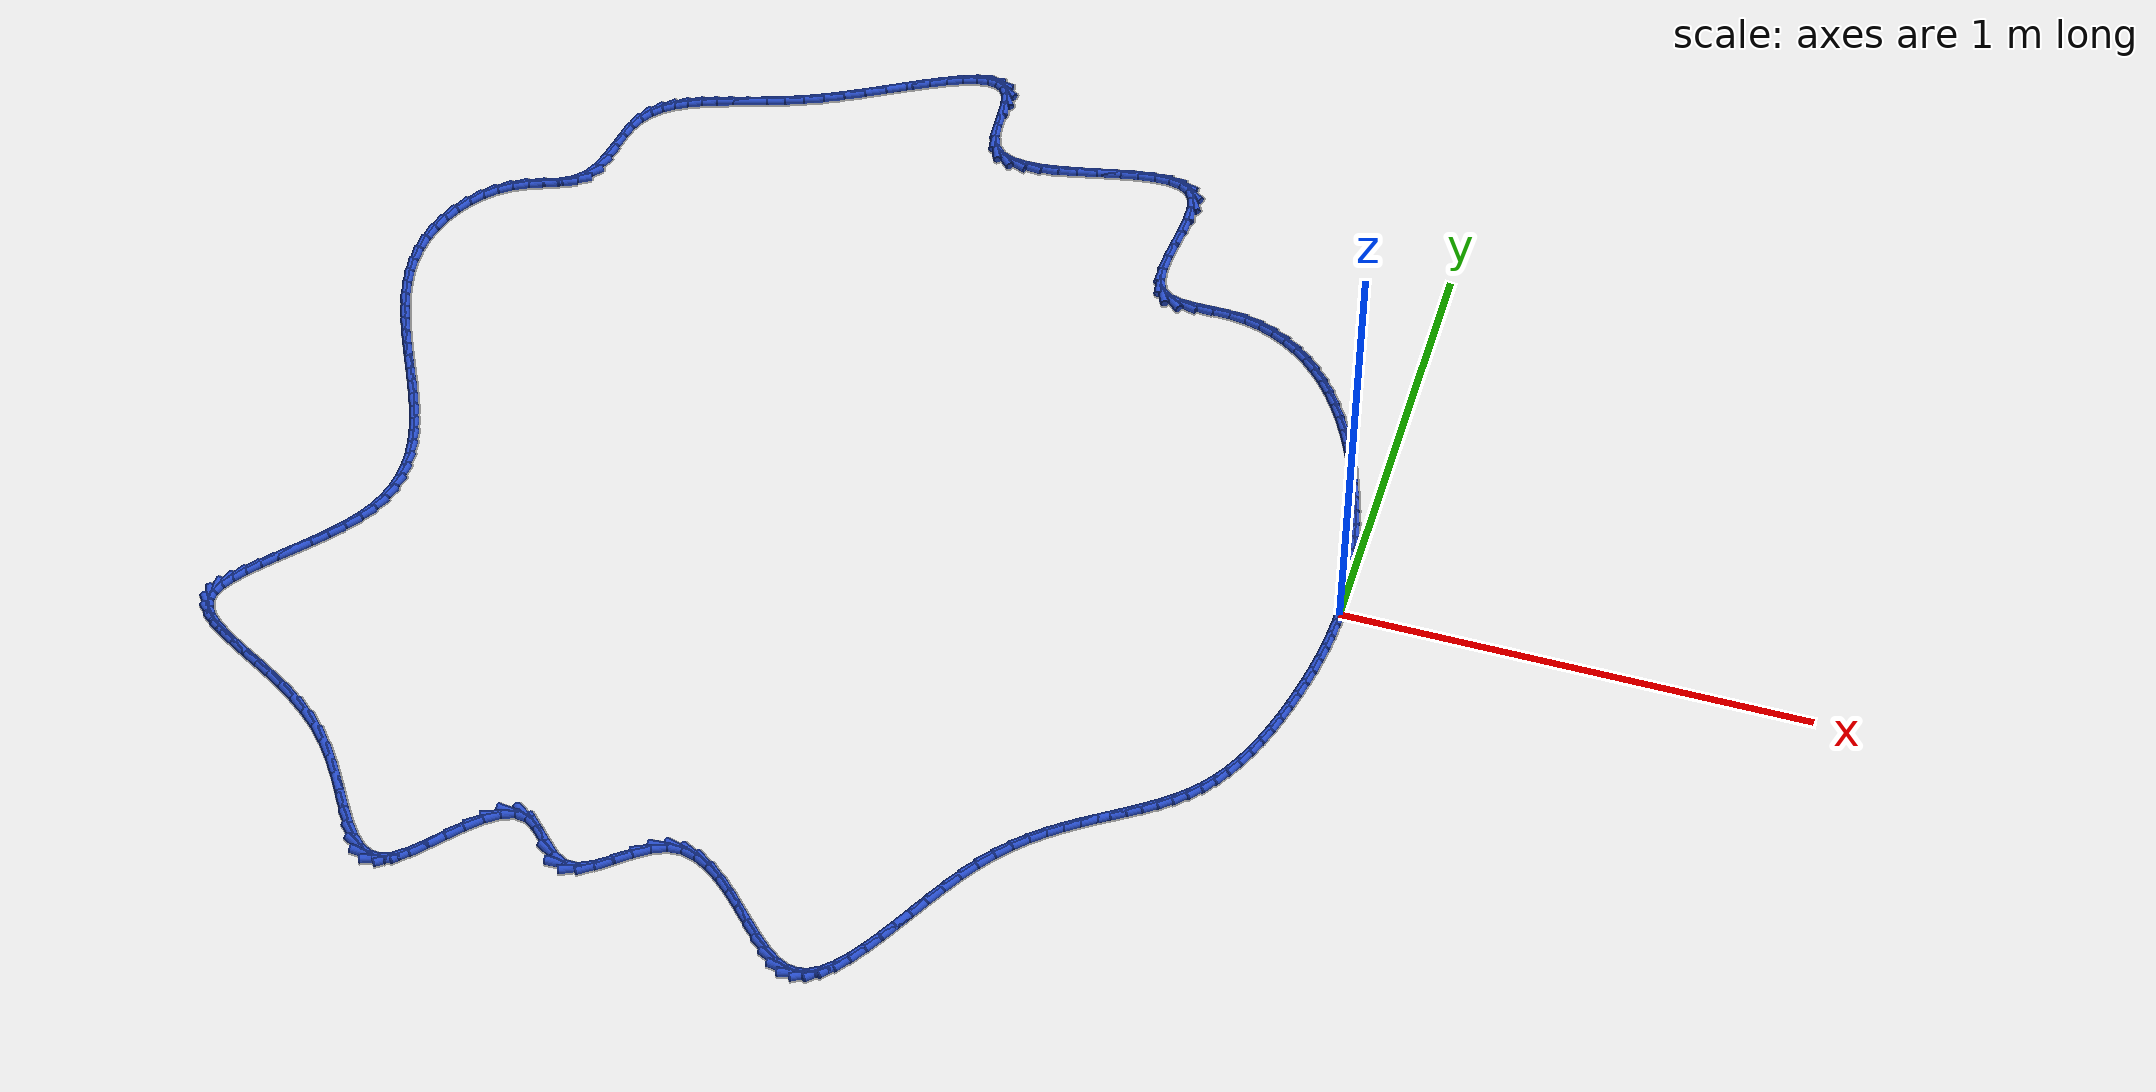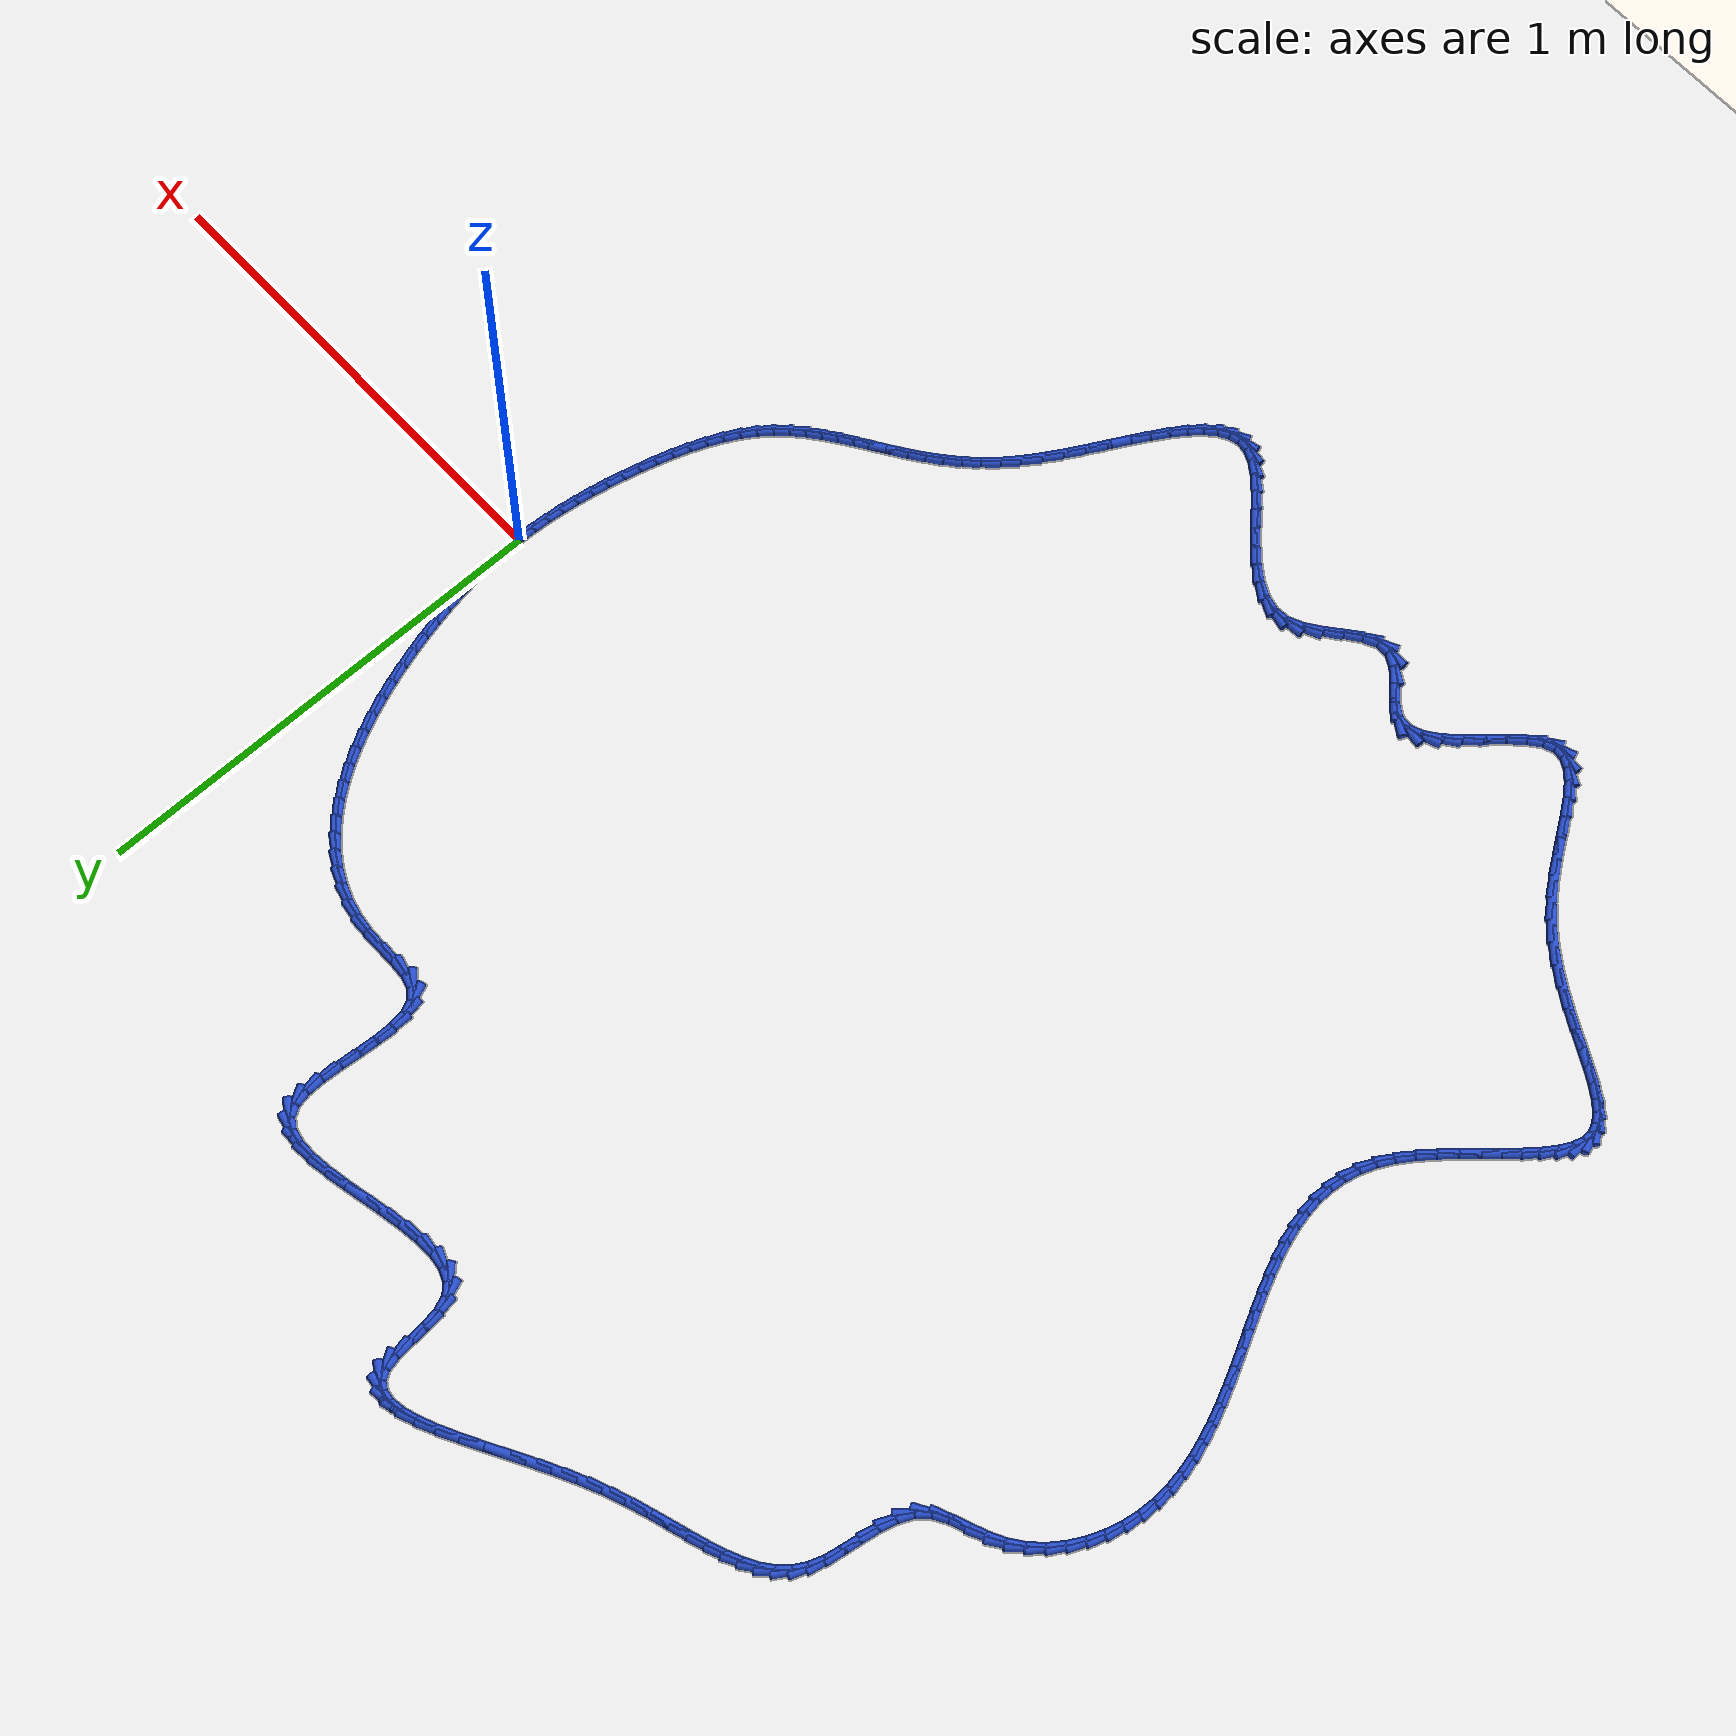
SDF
<sdf version="1.6">
 <world name="default">
  <light name="sun" type="directional">
   <pose>0 0 10 0 -0 0</pose>
   <diffuse>0.8 0.8 0.8 1</diffuse>
   <specular>0.2 0.2 0.2 1</specular>
   <attenuation>
    <range>1000</range>
    <constant>0.9</constant>
    <linear>0.01</linear>
    <quadratic>0.001</quadratic>
   </attenuation>
   <direction>-0.5 0.1 -0.9</direction>
  </light>
  <model name="ground_plane">
   <static>1</static>
   <link name="link">
    <collision name="collision">
     <geometry><plane><normal>0 0 1</normal><size>100 100</size></plane></geometry>
     <surface><friction><ode><mu>100</mu><mu2>50</mu2></ode></friction></surface>
    </collision>
    <visual name="visual">
     <cast_shadows>0</cast_shadows>
     <geometry><plane><normal>0 0 1</normal><size>100 100</size></plane></geometry>
     <material>
      <script><uri>file://media/materials/scripts/gazebo.material</uri><name>Gazebo/WhiteGlow</name></script>
     </material>
    </visual>
   </link>
  </model>
  <gravity>0 0 -9.8</gravity>
  <magnetic_field>6e-06 2.3e-05 -4.2e-05</magnetic_field>
  <atmosphere type="adiabatic"/>
  <physics name="default_physics" default="0" type="ode">
   <max_step_size>0.001</max_step_size>
   <real_time_factor>1</real_time_factor>
   <real_time_update_rate>1000</real_time_update_rate>
  </physics>
  <scene><ambient>0.4 0.4 0.4 1</ambient><background>0.7 0.7 0.7 1</background><shadows>1</shadows></scene>
  <spherical_coordinates>
   <surface_model>EARTH_WGS84</surface_model>
   <latitude_deg>0</latitude_deg>
   <longitude_deg>0</longitude_deg>
   <elevation>0</elevation>
   <heading_deg>0</heading_deg>
  </spherical_coordinates>
  <model name="line">
   <link name="link_0">
    <pose>2.168404344971009e-17 0.0 0.01 0 1.57 -1.5553201995796697</pose>
    <collision name="collision">
     <geometry><cylinder><radius>0.01</radius><length>0.08</length></cylinder></geometry>
    </collision>
    <visual name="visual">
     <material>
      <script><name>Gazebo/Blue</name><uri>file://media/materials/scripts/gazebo.material</uri></script>
     </material>
     <geometry><cylinder><radius>0.01</radius><length>0.08</length></cylinder></geometry>
    </visual>
   </link>
   <link name="link_1">
    <pose>-0.0005262779702996634 0.03400307751037581 0.01 0 1.57 -1.5172467446629432</pose>
    <collision name="collision">
     <geometry><cylinder><radius>0.01</radius><length>0.08</length></cylinder></geometry>
    </collision>
    <visual name="visual">
     <material>
      <script><name>Gazebo/Blue</name><uri>file://media/materials/scripts/gazebo.material</uri></script>
     </material>
     <geometry><cylinder><radius>0.01</radius><length>0.08</length></cylinder></geometry>
    </visual>
   </link>
   <link name="link_2">
    <pose>-0.002347161801183219 0.0679742669972863 0.01 0 1.57 -1.4803630752536083</pose>
    <collision name="collision">
     <geometry><cylinder><radius>0.01</radius><length>0.08</length></cylinder></geometry>
    </collision>
    <visual name="visual">
     <material>
      <script><name>Gazebo/Blue</name><uri>file://media/materials/scripts/gazebo.material</uri></script>
     </material>
     <geometry><cylinder><radius>0.01</radius><length>0.08</length></cylinder></geometry>
    </visual>
   </link>
   <link name="link_3">
    <pose>-0.005433390352669076 0.10200832716290426 0.01 0 1.57 -1.4450492172705172</pose>
    <collision name="collision">
     <geometry><cylinder><radius>0.01</radius><length>0.08</length></cylinder></geometry>
    </collision>
    <visual name="visual">
     <material>
      <script><name>Gazebo/Blue</name><uri>file://media/materials/scripts/gazebo.material</uri></script>
     </material>
     <geometry><cylinder><radius>0.01</radius><length>0.08</length></cylinder></geometry>
    </visual>
   </link>
   <link name="link_4">
    <pose>-0.009755702484775664 0.13620001670940232 0.01 0 1.57 -1.4116292390843488</pose>
    <collision name="collision">
     <geometry><cylinder><radius>0.01</radius><length>0.08</length></cylinder></geometry>
    </collision>
    <visual name="visual">
     <material>
      <script><name>Gazebo/Blue</name><uri>file://media/materials/scripts/gazebo.material</uri></script>
     </material>
     <geometry><cylinder><radius>0.01</radius><length>0.08</length></cylinder></geometry>
    </visual>
   </link>
   <link name="link_5">
    <pose>-0.01528483705752141 0.1706440943389534 0.01 0 1.57 -1.380362491238148</pose>
    <collision name="collision">
     <geometry><cylinder><radius>0.01</radius><length>0.08</length></cylinder></geometry>
    </collision>
    <visual name="visual">
     <material>
      <script><name>Gazebo/Blue</name><uri>file://media/materials/scripts/gazebo.material</uri></script>
     </material>
     <geometry><cylinder><radius>0.01</radius><length>0.08</length></cylinder></geometry>
    </visual>
   </link>
   <link name="link_6">
    <pose>-0.021991532930924748 0.20543531875373003 0.01 0 1.57 -1.3514401848331339</pose>
    <collision name="collision">
     <geometry><cylinder><radius>0.01</radius><length>0.08</length></cylinder></geometry>
    </collision>
    <visual name="visual">
     <material>
      <script><name>Gazebo/Blue</name><uri>file://media/materials/scripts/gazebo.material</uri></script>
     </material>
     <geometry><cylinder><radius>0.01</radius><length>0.08</length></cylinder></geometry>
    </visual>
   </link>
   <link name="link_7">
    <pose>-0.029846528965004105 0.24066844865590512 0.01 0 1.57 -1.3249818757967182</pose>
    <collision name="collision">
     <geometry><cylinder><radius>0.01</radius><length>0.08</length></cylinder></geometry>
    </collision>
    <visual name="visual">
     <material>
      <script><name>Gazebo/Blue</name><uri>file://media/materials/scripts/gazebo.material</uri></script>
     </material>
     <geometry><cylinder><radius>0.01</radius><length>0.08</length></cylinder></geometry>
    </visual>
   </link>
   <link name="link_8">
    <pose>-0.03882065354741122 0.27643786391770175 0.01 0 1.57 -1.2997533426891432</pose>
    <collision name="collision">
     <geometry><cylinder><radius>0.01</radius><length>0.08</length></cylinder></geometry>
    </collision>
    <visual name="visual">
     <material>
      <script><name>Gazebo/Blue</name><uri>file://media/materials/scripts/gazebo.material</uri></script>
     </material>
     <geometry><cylinder><radius>0.01</radius><length>0.08</length></cylinder></geometry>
    </visual>
   </link>
   <link name="link_9">
    <pose>-0.04890809222452517 0.3127391102197503 0.01 0 1.57 -1.2725872218309806</pose>
    <collision name="collision">
     <geometry><cylinder><radius>0.01</radius><length>0.08</length></cylinder></geometry>
    </collision>
    <visual name="visual">
     <material>
      <script><name>Gazebo/Blue</name><uri>file://media/materials/scripts/gazebo.material</uri></script>
     </material>
     <geometry><cylinder><radius>0.01</radius><length>0.08</length></cylinder></geometry>
    </visual>
   </link>
   <link name="link_10">
    <pose>-0.0601574773369932 0.3493373454220084 0.01 0 1.57 -1.2427075002954544</pose>
    <collision name="collision">
     <geometry><cylinder><radius>0.01</radius><length>0.08</length></cylinder></geometry>
    </collision>
    <visual name="visual">
     <material>
      <script><name>Gazebo/Blue</name><uri>file://media/materials/scripts/gazebo.material</uri></script>
     </material>
     <geometry><cylinder><radius>0.01</radius><length>0.08</length></cylinder></geometry>
    </visual>
   </link>
   <link name="link_11">
    <pose>-0.07262518406984488 0.3859649640773 0.01 0 1.57 -1.2097056486750113</pose>
    <collision name="collision">
     <geometry><cylinder><radius>0.01</radius><length>0.08</length></cylinder></geometry>
    </collision>
    <visual name="visual">
     <material>
      <script><name>Gazebo/Blue</name><uri>file://media/materials/scripts/gazebo.material</uri></script>
     </material>
     <geometry><cylinder><radius>0.01</radius><length>0.08</length></cylinder></geometry>
    </visual>
   </link>
   <link name="link_12">
    <pose>-0.08636758760810971 0.4223543607384489 0.01 0 1.57 -1.1731120403888633</pose>
    <collision name="collision">
     <geometry><cylinder><radius>0.01</radius><length>0.08</length></cylinder></geometry>
    </collision>
    <visual name="visual">
     <material>
      <script><name>Gazebo/Blue</name><uri>file://media/materials/scripts/gazebo.material</uri></script>
     </material>
     <geometry><cylinder><radius>0.01</radius><length>0.08</length></cylinder></geometry>
    </visual>
   </link>
   <link name="link_13">
    <pose>-0.10144106313681722 0.458237929958279 0.01 0 1.57 -1.1323886352628987</pose>
    <collision name="collision">
     <geometry><cylinder><radius>0.01</radius><length>0.08</length></cylinder></geometry>
    </collision>
    <visual name="visual">
     <material>
      <script><name>Gazebo/Blue</name><uri>file://media/materials/scripts/gazebo.material</uri></script>
     </material>
     <geometry><cylinder><radius>0.01</radius><length>0.08</length></cylinder></geometry>
    </visual>
   </link>
   <link name="link_14">
    <pose>-0.11790198584099705 0.49334806628961436 0.01 0 1.57 -1.0869244574376047</pose>
    <collision name="collision">
     <geometry><cylinder><radius>0.01</radius><length>0.08</length></cylinder></geometry>
    </collision>
    <visual name="visual">
     <material>
      <script><name>Gazebo/Blue</name><uri>file://media/materials/scripts/gazebo.material</uri></script>
     </material>
     <geometry><cylinder><radius>0.01</radius><length>0.08</length></cylinder></geometry>
    </visual>
   </link>
   <link name="link_15">
    <pose>-0.1358067309056786 0.5274171642852787 0.01 0 1.57 -1.0360369138510355</pose>
    <collision name="collision">
     <geometry><cylinder><radius>0.01</radius><length>0.08</length></cylinder></geometry>
    </collision>
    <visual name="visual">
     <material>
      <script><name>Gazebo/Blue</name><uri>file://media/materials/scripts/gazebo.material</uri></script>
     </material>
     <geometry><cylinder><radius>0.01</radius><length>0.08</length></cylinder></geometry>
    </visual>
   </link>
   <link name="link_16">
    <pose>-0.1552116735158916 0.5601776184980961 0.01 0 1.57 -0.9789839347264426</pose>
    <collision name="collision">
     <geometry><cylinder><radius>0.01</radius><length>0.08</length></cylinder></geometry>
    </collision>
    <visual name="visual">
     <material>
      <script><name>Gazebo/Blue</name><uri>file://media/materials/scripts/gazebo.material</uri></script>
     </material>
     <geometry><cylinder><radius>0.01</radius><length>0.08</length></cylinder></geometry>
    </visual>
   </link>
   <link name="link_17">
    <pose>-0.1761731888566654 0.5913618234808902 0.01 0 1.57 -0.9149944381178255</pose>
    <collision name="collision">
     <geometry><cylinder><radius>0.01</radius><length>0.08</length></cylinder></geometry>
    </collision>
    <visual name="visual">
     <material>
      <script><name>Gazebo/Blue</name><uri>file://media/materials/scripts/gazebo.material</uri></script>
     </material>
     <geometry><cylinder><radius>0.01</radius><length>0.08</length></cylinder></geometry>
    </visual>
   </link>
   <link name="link_18">
    <pose>-0.19874765211302972 0.6207021737864852 0.01 0 1.57 -0.8433272272003393</pose>
    <collision name="collision">
     <geometry><cylinder><radius>0.01</radius><length>0.08</length></cylinder></geometry>
    </collision>
    <visual name="visual">
     <material>
      <script><name>Gazebo/Blue</name><uri>file://media/materials/scripts/gazebo.material</uri></script>
     </material>
     <geometry><cylinder><radius>0.01</radius><length>0.08</length></cylinder></geometry>
    </visual>
   </link>
   <link name="link_19">
    <pose>-0.2229914384700139 0.6479310639677045 0.01 0 1.57 -0.7633695499647677</pose>
    <collision name="collision">
     <geometry><cylinder><radius>0.01</radius><length>0.08</length></cylinder></geometry>
    </collision>
    <visual name="visual">
     <material>
      <script><name>Gazebo/Blue</name><uri>file://media/materials/scripts/gazebo.material</uri></script>
     </material>
     <geometry><cylinder><radius>0.01</radius><length>0.08</length></cylinder></geometry>
    </visual>
   </link>
   <link name="link_20">
    <pose>-0.24896092311264773 0.6727808885773727 0.01 0 1.57 -0.6747828435483268</pose>
    <collision name="collision">
     <geometry><cylinder><radius>0.01</radius><length>0.08</length></cylinder></geometry>
    </collision>
    <visual name="visual">
     <material>
      <script><name>Gazebo/Blue</name><uri>file://media/materials/scripts/gazebo.material</uri></script>
     </material>
     <geometry><cylinder><radius>0.01</radius><length>0.08</length></cylinder></geometry>
    </visual>
   </link>
   <link name="link_21">
    <pose>-0.2767124812259606 0.6949840421683133 0.01 0 1.57 -0.5776896192459179</pose>
    <collision name="collision">
     <geometry><cylinder><radius>0.01</radius><length>0.08</length></cylinder></geometry>
    </collision>
    <visual name="visual">
     <material>
      <script><name>Gazebo/Blue</name><uri>file://media/materials/scripts/gazebo.material</uri></script>
     </material>
     <geometry><cylinder><radius>0.01</radius><length>0.08</length></cylinder></geometry>
    </visual>
   </link>
   <link name="link_22">
    <pose>-0.3063024879949821 0.7142729192933501 0.01 0 1.57 -0.47286827136064236</pose>
    <collision name="collision">
     <geometry><cylinder><radius>0.01</radius><length>0.08</length></cylinder></geometry>
    </collision>
    <visual name="visual">
     <material>
      <script><name>Gazebo/Blue</name><uri>file://media/materials/scripts/gazebo.material</uri></script>
     </material>
     <geometry><cylinder><radius>0.01</radius><length>0.08</length></cylinder></geometry>
    </visual>
   </link>
   <link name="link_23">
    <pose>-0.3377873186047418 0.7303799145053075 0.01 0 1.57 -0.3618871780111352</pose>
    <collision name="collision">
     <geometry><cylinder><radius>0.01</radius><length>0.08</length></cylinder></geometry>
    </collision>
    <visual name="visual">
     <material>
      <script><name>Gazebo/Blue</name><uri>file://media/materials/scripts/gazebo.material</uri></script>
     </material>
     <geometry><cylinder><radius>0.01</radius><length>0.08</length></cylinder></geometry>
    </visual>
   </link>
   <link name="link_24">
    <pose>-0.37122334824026915 0.7430374223570085 0.01 0 1.57 -0.24708897873216454</pose>
    <collision name="collision">
     <geometry><cylinder><radius>0.01</radius><length>0.08</length></cylinder></geometry>
    </collision>
    <visual name="visual">
     <material>
      <script><name>Gazebo/Blue</name><uri>file://media/materials/scripts/gazebo.material</uri></script>
     </material>
     <geometry><cylinder><radius>0.01</radius><length>0.08</length></cylinder></geometry>
    </visual>
   </link>
   <link name="link_25">
    <pose>-0.4066669520865937 0.751977837401278 0.01 0 1.57 -0.1313649384565871</pose>
    <collision name="collision">
     <geometry><cylinder><radius>0.01</radius><length>0.08</length></cylinder></geometry>
    </collision>
    <visual name="visual">
     <material>
      <script><name>Gazebo/Blue</name><uri>file://media/materials/scripts/gazebo.material</uri></script>
     </material>
     <geometry><cylinder><radius>0.01</radius><length>0.08</length></cylinder></geometry>
    </visual>
   </link>
   <link name="link_26">
    <pose>-0.4441745053287452 0.7569335541909392 0.01 0 1.57 -0.027857202016492742</pose>
    <collision name="collision">
     <geometry><cylinder><radius>0.01</radius><length>0.08</length></cylinder></geometry>
    </collision>
    <visual name="visual">
     <material>
      <script><name>Gazebo/Blue</name><uri>file://media/materials/scripts/gazebo.material</uri></script>
     </material>
     <geometry><cylinder><radius>0.01</radius><length>0.08</length></cylinder></geometry>
    </visual>
   </link>
   <link name="link_27">
    <pose>-0.483497100544818 0.7580292551143135 0.01 0 1.57 0.003887102109623575</pose>
    <collision name="collision">
     <geometry><cylinder><radius>0.01</radius><length>0.08</length></cylinder></geometry>
    </collision>
    <visual name="visual">
     <material>
      <script><name>Gazebo/Blue</name><uri>file://media/materials/scripts/gazebo.material</uri></script>
     </material>
     <geometry><cylinder><radius>0.01</radius><length>0.08</length></cylinder></geometry>
    </visual>
   </link>
   <link name="link_28">
    <pose>-0.5224494708221701 0.7578778425110401 0.01 0 1.57 -0.06128359200635334</pose>
    <collision name="collision">
     <geometry><cylinder><radius>0.01</radius><length>0.08</length></cylinder></geometry>
    </collision>
    <visual name="visual">
     <material>
      <script><name>Gazebo/Blue</name><uri>file://media/materials/scripts/gazebo.material</uri></script>
     </material>
     <geometry><cylinder><radius>0.01</radius><length>0.08</length></cylinder></geometry>
    </visual>
   </link>
   <link name="link_29">
    <pose>-0.5580895291692867 0.760064731742652 0.01 0 1.57 -0.26938697486365387</pose>
    <collision name="collision">
     <geometry><cylinder><radius>0.01</radius><length>0.08</length></cylinder></geometry>
    </collision>
    <visual name="visual">
     <material>
      <script><name>Gazebo/Blue</name><uri>file://media/materials/scripts/gazebo.material</uri></script>
     </material>
     <geometry><cylinder><radius>0.01</radius><length>0.08</length></cylinder></geometry>
    </visual>
   </link>
   <link name="link_30">
    <pose>-0.5874734441545285 0.7681775797744445 0.01 0 1.57 -0.7060367075536731</pose>
    <collision name="collision">
     <geometry><cylinder><radius>0.01</radius><length>0.08</length></cylinder></geometry>
    </collision>
    <visual name="visual">
     <material>
      <script><name>Gazebo/Blue</name><uri>file://media/materials/scripts/gazebo.material</uri></script>
     </material>
     <geometry><cylinder><radius>0.01</radius><length>0.08</length></cylinder></geometry>
    </visual>
   </link>
   <link name="link_31">
    <pose>-0.6078645218850702 0.7855642502644155 0.01 0 1.57 -1.1673834614039085</pose>
    <collision name="collision">
     <geometry><cylinder><radius>0.01</radius><length>0.08</length></cylinder></geometry>
    </collision>
    <visual name="visual">
     <material>
      <script><name>Gazebo/Blue</name><uri>file://media/materials/scripts/gazebo.material</uri></script>
     </material>
     <geometry><cylinder><radius>0.01</radius><length>0.08</length></cylinder></geometry>
    </visual>
   </link>
   <link name="link_32">
    <pose>-0.6193014164403144 0.812359718115688 0.01 0 1.57 -1.439282408955972</pose>
    <collision name="collision">
     <geometry><cylinder><radius>0.01</radius><length>0.08</length></cylinder></geometry>
    </collision>
    <visual name="visual">
     <material>
      <script><name>Gazebo/Blue</name><uri>file://media/materials/scripts/gazebo.material</uri></script>
     </material>
     <geometry><cylinder><radius>0.01</radius><length>0.08</length></cylinder></geometry>
    </visual>
   </link>
   <link name="link_33">
    <pose>-0.6238047725097432 0.8464045016777911 0.01 0 1.57 1.5614137025409496</pose>
    <collision name="collision">
     <geometry><cylinder><radius>0.01</radius><length>0.08</length></cylinder></geometry>
    </collision>
    <visual name="visual">
     <material>
      <script><name>Gazebo/Blue</name><uri>file://media/materials/scripts/gazebo.material</uri></script>
     </material>
     <geometry><cylinder><radius>0.01</radius><length>0.08</length></cylinder></geometry>
    </visual>
   </link>
   <link name="link_34">
    <pose>-0.6234380412922119 0.8854895642340136 0.01 0 1.57 1.4952332428060828</pose>
    <collision name="collision">
     <geometry><cylinder><radius>0.01</radius><length>0.08</length></cylinder></geometry>
    </collision>
    <visual name="visual">
     <material>
      <script><name>Gazebo/Blue</name><uri>file://media/materials/scripts/gazebo.material</uri></script>
     </material>
     <geometry><cylinder><radius>0.01</radius><length>0.08</length></cylinder></geometry>
    </visual>
   </link>
   <link name="link_35">
    <pose>-0.6202646739865761 0.9274058690676447 0.01 0 1.57 1.4789844318858119</pose>
    <collision name="collision">
     <geometry><cylinder><radius>0.01</radius><length>0.08</length></cylinder></geometry>
    </collision>
    <visual name="visual">
     <material>
      <script><name>Gazebo/Blue</name><uri>file://media/materials/scripts/gazebo.material</uri></script>
     </material>
     <geometry><cylinder><radius>0.01</radius><length>0.08</length></cylinder></geometry>
    </visual>
   </link>
   <link name="link_36">
    <pose>-0.616348121791691 0.9699443794619735 0.01 0 1.57 1.5074822993449497</pose>
    <collision name="collision">
     <geometry><cylinder><radius>0.01</radius><length>0.08</length></cylinder></geometry>
    </collision>
    <visual name="visual">
     <material>
      <script><name>Gazebo/Blue</name><uri>file://media/materials/scripts/gazebo.material</uri></script>
     </material>
     <geometry><cylinder><radius>0.01</radius><length>0.08</length></cylinder></geometry>
    </visual>
   </link>
   <link name="link_37">
    <pose>-0.6137518359064121 1.0108960587002893 0.01 0 1.57 -1.5496068078588994</pose>
    <collision name="collision">
     <geometry><cylinder><radius>0.01</radius><length>0.08</length></cylinder></geometry>
    </collision>
    <visual name="visual">
     <material>
      <script><name>Gazebo/Blue</name><uri>file://media/materials/scripts/gazebo.material</uri></script>
     </material>
     <geometry><cylinder><radius>0.01</radius><length>0.08</length></cylinder></geometry>
    </visual>
   </link>
   <link name="link_38">
    <pose>-0.6145392675295944 1.0480518700658805 0.01 0 1.57 -1.3732643696717592</pose>
    <collision name="collision">
     <geometry><cylinder><radius>0.01</radius><length>0.08</length></cylinder></geometry>
    </collision>
    <visual name="visual">
     <material>
      <script><name>Gazebo/Blue</name><uri>file://media/materials/scripts/gazebo.material</uri></script>
     </material>
     <geometry><cylinder><radius>0.01</radius><length>0.08</length></cylinder></geometry>
    </visual>
   </link>
   <link name="link_39">
    <pose>-0.6207738678600939 1.0792027768420374 0.01 0 1.57 -1.032121564579606</pose>
    <collision name="collision">
     <geometry><cylinder><radius>0.01</radius><length>0.08</length></cylinder></geometry>
    </collision>
    <visual name="visual">
     <material>
      <script><name>Gazebo/Blue</name><uri>file://media/materials/scripts/gazebo.material</uri></script>
     </material>
     <geometry><cylinder><radius>0.01</radius><length>0.08</length></cylinder></geometry>
    </visual>
   </link>
   <link name="link_40">
    <pose>-0.6344964567202794 1.1021644709265332 0.01 0 1.57 -0.5665945314020063</pose>
    <collision name="collision">
     <geometry><cylinder><radius>0.01</radius><length>0.08</length></cylinder></geometry>
    </collision>
    <visual name="visual">
     <material>
      <script><name>Gazebo/Blue</name><uri>file://media/materials/scripts/gazebo.material</uri></script>
     </material>
     <geometry><cylinder><radius>0.01</radius><length>0.08</length></cylinder></geometry>
    </visual>
   </link>
   <link name="link_41">
    <pose>-0.6564731460597895 1.1161454786117004 0.01 0 1.57 -0.21399571540646548</pose>
    <collision name="collision">
     <geometry><cylinder><radius>0.01</radius><length>0.08</length></cylinder></geometry>
    </collision>
    <visual name="visual">
     <material>
      <script><name>Gazebo/Blue</name><uri>file://media/materials/scripts/gazebo.material</uri></script>
     </material>
     <geometry><cylinder><radius>0.01</radius><length>0.08</length></cylinder></geometry>
    </visual>
   </link>
   <link name="link_42">
    <pose>-0.6855406475530186 1.122462522994577 0.01 0 1.57 -0.004172750003612432</pose>
    <collision name="collision">
     <geometry><cylinder><radius>0.01</radius><length>0.08</length></cylinder></geometry>
    </collision>
    <visual name="visual">
     <material>
      <script><name>Gazebo/Blue</name><uri>file://media/materials/scripts/gazebo.material</uri></script>
     </material>
     <geometry><cylinder><radius>0.01</radius><length>0.08</length></cylinder></geometry>
    </visual>
   </link>
   <link name="link_43">
    <pose>-0.7203750096974166 1.12260787892298 0.01 0 1.57 0.11492848517439634</pose>
    <collision name="collision">
     <geometry><cylinder><radius>0.01</radius><length>0.08</length></cylinder></geometry>
    </collision>
    <visual name="visual">
     <material>
      <script><name>Gazebo/Blue</name><uri>file://media/materials/scripts/gazebo.material</uri></script>
     </material>
     <geometry><cylinder><radius>0.01</radius><length>0.08</length></cylinder></geometry>
    </visual>
   </link>
   <link name="link_44">
    <pose>-0.7596522809904332 1.1180738212447265 0.01 0 1.57 0.18014553520085633</pose>
    <collision name="collision">
     <geometry><cylinder><radius>0.01</radius><length>0.08</length></cylinder></geometry>
    </collision>
    <visual name="visual">
     <material>
      <script><name>Gazebo/Blue</name><uri>file://media/materials/scripts/gazebo.material</uri></script>
     </material>
     <geometry><cylinder><radius>0.01</radius><length>0.08</length></cylinder></geometry>
    </visual>
   </link>
   <link name="link_45">
    <pose>-0.8020485099295177 1.110352624807633 0.01 0 1.57 0.20993576550918802</pose>
    <collision name="collision">
     <geometry><cylinder><radius>0.01</radius><length>0.08</length></cylinder></geometry>
    </collision>
    <visual name="visual">
     <material>
      <script><name>Gazebo/Blue</name><uri>file://media/materials/scripts/gazebo.material</uri></script>
     </material>
     <geometry><cylinder><radius>0.01</radius><length>0.08</length></cylinder></geometry>
    </visual>
   </link>
   <link name="link_46">
    <pose>-0.8462397450121197 1.1009365644595168 0.01 0 1.57 0.21212405250788746</pose>
    <collision name="collision">
     <geometry><cylinder><radius>0.01</radius><length>0.08</length></cylinder></geometry>
    </collision>
    <visual name="visual">
     <material>
      <script><name>Gazebo/Blue</name><uri>file://media/materials/scripts/gazebo.material</uri></script>
     </material>
     <geometry><cylinder><radius>0.01</radius><length>0.08</length></cylinder></geometry>
    </visual>
   </link>
   <link name="link_47">
    <pose>-0.8909020347356889 1.0913179150481942 0.01 0 1.57 0.18787604139338507</pose>
    <collision name="collision">
     <geometry><cylinder><radius>0.01</radius><length>0.08</length></cylinder></geometry>
    </collision>
    <visual name="visual">
     <material>
      <script><name>Gazebo/Blue</name><uri>file://media/materials/scripts/gazebo.material</uri></script>
     </material>
     <geometry><cylinder><radius>0.01</radius><length>0.08</length></cylinder></geometry>
    </visual>
   </link>
   <link name="link_48">
    <pose>-0.9347114275976749 1.0829889514214823 0.01 0 1.57 0.13245706130021845</pose>
    <collision name="collision">
     <geometry><cylinder><radius>0.01</radius><length>0.08</length></cylinder></geometry>
    </collision>
    <visual name="visual">
     <material>
      <script><name>Gazebo/Blue</name><uri>file://media/materials/scripts/gazebo.material</uri></script>
     </material>
     <geometry><cylinder><radius>0.01</radius><length>0.08</length></cylinder></geometry>
    </visual>
   </link>
   <link name="link_49">
    <pose>-0.9763439720955264 1.0774419484271978 0.01 0 1.57 0.03336577379109931</pose>
    <collision name="collision">
     <geometry><cylinder><radius>0.01</radius><length>0.08</length></cylinder></geometry>
    </collision>
    <visual name="visual">
     <material>
      <script><name>Gazebo/Blue</name><uri>file://media/materials/scripts/gazebo.material</uri></script>
     </material>
     <geometry><cylinder><radius>0.01</radius><length>0.08</length></cylinder></geometry>
    </visual>
   </link>
   <link name="link_50">
    <pose>-1.014475716726694 1.0761691809131573 0.01 0 1.57 -0.13410907635341549</pose>
    <collision name="collision">
     <geometry><cylinder><radius>0.01</radius><length>0.08</length></cylinder></geometry>
    </collision>
    <visual name="visual">
     <material>
      <script><name>Gazebo/Blue</name><uri>file://media/materials/scripts/gazebo.material</uri></script>
     </material>
     <geometry><cylinder><radius>0.01</radius><length>0.08</length></cylinder></geometry>
    </visual>
   </link>
   <link name="link_51">
    <pose>-1.0477827099886272 1.080662923727178 0.01 0 1.57 -0.4084097208299337</pose>
    <collision name="collision">
     <geometry><cylinder><radius>0.01</radius><length>0.08</length></cylinder></geometry>
    </collision>
    <visual name="visual">
     <material>
      <script><name>Gazebo/Blue</name><uri>file://media/materials/scripts/gazebo.material</uri></script>
     </material>
     <geometry><cylinder><radius>0.01</radius><length>0.08</length></cylinder></geometry>
    </visual>
   </link>
   <link name="link_52">
    <pose>-1.074941000378775 1.0924154517170765 0.01 0 1.57 -0.8057478742179125</pose>
    <collision name="collision">
     <geometry><cylinder><radius>0.01</radius><length>0.08</length></cylinder></geometry>
    </collision>
    <visual name="visual">
     <material>
      <script><name>Gazebo/Blue</name><uri>file://media/materials/scripts/gazebo.material</uri></script>
     </material>
     <geometry><cylinder><radius>0.01</radius><length>0.08</length></cylinder></geometry>
    </visual>
   </link>
   <link name="link_53">
    <pose>-1.0946266363945873 1.1129190397306699 0.01 0 1.57 -1.2043488727486766</pose>
    <collision name="collision">
     <geometry><cylinder><radius>0.01</radius><length>0.08</length></cylinder></geometry>
    </collision>
    <visual name="visual">
     <material>
      <script><name>Gazebo/Blue</name><uri>file://media/materials/scripts/gazebo.material</uri></script>
     </material>
     <geometry><cylinder><radius>0.01</radius><length>0.08</length></cylinder></geometry>
    </visual>
   </link>
   <link name="link_54">
    <pose>-1.1061241487863465 1.1428775026969902 0.01 0 1.57 -1.4189695658748431</pose>
    <collision name="collision">
     <geometry><cylinder><radius>0.01</radius><length>0.08</length></cylinder></geometry>
    </collision>
    <visual name="visual">
     <material>
      <script><name>Gazebo/Blue</name><uri>file://media/materials/scripts/gazebo.material</uri></script>
     </material>
     <geometry><cylinder><radius>0.01</radius><length>0.08</length></cylinder></geometry>
    </visual>
   </link>
   <link name="link_55">
    <pose>-1.1116758356326157 1.1791620359796127 0.01 0 1.57 -1.4992678715452665</pose>
    <collision name="collision">
     <geometry><cylinder><radius>0.01</radius><length>0.08</length></cylinder></geometry>
    </collision>
    <visual name="visual">
     <material>
      <script><name>Gazebo/Blue</name><uri>file://media/materials/scripts/gazebo.material</uri></script>
     </material>
     <geometry><cylinder><radius>0.01</radius><length>0.08</length></cylinder></geometry>
    </visual>
   </link>
   <link name="link_56">
    <pose>-1.114421414229995 1.2174809759097003 0.01 0 1.57 -1.4856100562711685</pose>
    <collision name="collision">
     <geometry><cylinder><radius>0.01</radius><length>0.08</length></cylinder></geometry>
    </collision>
    <visual name="visual">
     <material>
      <script><name>Gazebo/Blue</name><uri>file://media/materials/scripts/gazebo.material</uri></script>
     </material>
     <geometry><cylinder><radius>0.01</radius><length>0.08</length></cylinder></geometry>
    </visual>
   </link>
   <link name="link_57">
    <pose>-1.1175008044849892 1.2535423962802963 0.01 0 1.57 -1.3523575630717317</pose>
    <collision name="collision">
     <geometry><cylinder><radius>0.01</radius><length>0.08</length></cylinder></geometry>
    </collision>
    <visual name="visual">
     <material>
      <script><name>Gazebo/Blue</name><uri>file://media/materials/scripts/gazebo.material</uri></script>
     </material>
     <geometry><cylinder><radius>0.01</radius><length>0.08</length></cylinder></geometry>
    </visual>
   </link>
   <link name="link_58">
    <pose>-1.1240523881400692 1.2830566021816074 0.01 0 1.57 -1.0199769849017297</pose>
    <collision name="collision">
     <geometry><cylinder><radius>0.01</radius><length>0.08</length></cylinder></geometry>
    </collision>
    <visual name="visual">
     <material>
      <script><name>Gazebo/Blue</name><uri>file://media/materials/scripts/gazebo.material</uri></script>
     </material>
     <geometry><cylinder><radius>0.01</radius><length>0.08</length></cylinder></geometry>
    </visual>
   </link>
   <link name="link_59">
    <pose>-1.1363208790384876 1.3030302745196618 0.01 0 1.57 -0.5489929953946124</pose>
    <collision name="collision">
     <geometry><cylinder><radius>0.01</radius><length>0.08</length></cylinder></geometry>
    </collision>
    <visual name="visual">
     <material>
      <script><name>Gazebo/Blue</name><uri>file://media/materials/scripts/gazebo.material</uri></script>
     </material>
     <geometry><cylinder><radius>0.01</radius><length>0.08</length></cylinder></geometry>
    </visual>
   </link>
   <link name="link_60">
    <pose>-1.1541579107799853 1.3139415530675986 0.01 0 1.57 -0.1262654930091497</pose>
    <collision name="collision">
     <geometry><cylinder><radius>0.01</radius><length>0.08</length></cylinder></geometry>
    </collision>
    <visual name="visual">
     <material>
      <script><name>Gazebo/Blue</name><uri>file://media/materials/scripts/gazebo.material</uri></script>
     </material>
     <geometry><cylinder><radius>0.01</radius><length>0.08</length></cylinder></geometry>
    </visual>
   </link>
   <link name="link_61">
    <pose>-1.1770187691772234 1.3168435290836418 0.01 0 1.57 0.14721683500835966</pose>
    <collision name="collision">
     <geometry><cylinder><radius>0.01</radius><length>0.08</length></cylinder></geometry>
    </collision>
    <visual name="visual">
     <material>
      <script><name>Gazebo/Blue</name><uri>file://media/materials/scripts/gazebo.material</uri></script>
     </material>
     <geometry><cylinder><radius>0.01</radius><length>0.08</length></cylinder></geometry>
    </visual>
   </link>
   <link name="link_62">
    <pose>-1.204358740042859 1.3127892938260133 0.01 0 1.57 0.30823916741620105</pose>
    <collision name="collision">
     <geometry><cylinder><radius>0.01</radius><length>0.08</length></cylinder></geometry>
    </collision>
    <visual name="visual">
     <material>
      <script><name>Gazebo/Blue</name><uri>file://media/materials/scripts/gazebo.material</uri></script>
     </material>
     <geometry><cylinder><radius>0.01</radius><length>0.08</length></cylinder></geometry>
    </visual>
   </link>
   <link name="link_63">
    <pose>-1.235633109189553 1.302831938552937 0.01 0 1.57 0.4037057664045933</pose>
    <collision name="collision">
     <geometry><cylinder><radius>0.01</radius><length>0.08</length></cylinder></geometry>
    </collision>
    <visual name="visual">
     <material>
      <script><name>Gazebo/Blue</name><uri>file://media/materials/scripts/gazebo.material</uri></script>
     </material>
     <geometry><cylinder><radius>0.01</radius><length>0.08</length></cylinder></geometry>
    </visual>
   </link>
   <link name="link_64">
    <pose>-1.270297162429964 1.2880245545226359 0.01 0 1.57 0.4604391977581708</pose>
    <collision name="collision">
     <geometry><cylinder><radius>0.01</radius><length>0.08</length></cylinder></geometry>
    </collision>
    <visual name="visual">
     <material>
      <script><name>Gazebo/Blue</name><uri>file://media/materials/scripts/gazebo.material</uri></script>
     </material>
     <geometry><cylinder><radius>0.01</radius><length>0.08</length></cylinder></geometry>
    </visual>
   </link>
   <link name="link_65">
    <pose>-1.3078061855767507 1.2694202329933326 0.01 0 1.57 0.49223395962969607</pose>
    <collision name="collision">
     <geometry><cylinder><radius>0.01</radius><length>0.08</length></cylinder></geometry>
    </collision>
    <visual name="visual">
     <material>
      <script><name>Gazebo/Blue</name><uri>file://media/materials/scripts/gazebo.material</uri></script>
     </material>
     <geometry><cylinder><radius>0.01</radius><length>0.08</length></cylinder></geometry>
    </visual>
   </link>
   <link name="link_66">
    <pose>-1.3476154644425735 1.2480720652232493 0.01 0 1.57 0.5061301447515708</pose>
    <collision name="collision">
     <geometry><cylinder><radius>0.01</radius><length>0.08</length></cylinder></geometry>
    </collision>
    <visual name="visual">
     <material>
      <script><name>Gazebo/Blue</name><uri>file://media/materials/scripts/gazebo.material</uri></script>
     </material>
     <geometry><cylinder><radius>0.01</radius><length>0.08</length></cylinder></geometry>
    </visual>
   </link>
   <link name="link_67">
    <pose>-1.3891802848400907 1.2250331424706105 0.01 0 1.57 0.5055311294043117</pose>
    <collision name="collision">
     <geometry><cylinder><radius>0.01</radius><length>0.08</length></cylinder></geometry>
    </collision>
    <visual name="visual">
     <material>
      <script><name>Gazebo/Blue</name><uri>file://media/materials/scripts/gazebo.material</uri></script>
     </material>
     <geometry><cylinder><radius>0.01</radius><length>0.08</length></cylinder></geometry>
    </visual>
   </link>
   <link name="link_68">
    <pose>-1.4319559325819622 1.2013565559936379 0.01 0 1.57 0.4916085973503633</pose>
    <collision name="collision">
     <geometry><cylinder><radius>0.01</radius><length>0.08</length></cylinder></geometry>
    </collision>
    <visual name="visual">
     <material>
      <script><name>Gazebo/Blue</name><uri>file://media/materials/scripts/gazebo.material</uri></script>
     </material>
     <geometry><cylinder><radius>0.01</radius><length>0.08</length></cylinder></geometry>
    </visual>
   </link>
   <link name="link_69">
    <pose>-1.4753976934808466 1.1780953970505554 0.01 0 1.57 0.46385069974920246</pose>
    <collision name="collision">
     <geometry><cylinder><radius>0.01</radius><length>0.08</length></cylinder></geometry>
    </collision>
    <visual name="visual">
     <material>
      <script><name>Gazebo/Blue</name><uri>file://media/materials/scripts/gazebo.material</uri></script>
     </material>
     <geometry><cylinder><radius>0.01</radius><length>0.08</length></cylinder></geometry>
    </visual>
   </link>
   <link name="link_70">
    <pose>-1.5189608533494043 1.1563027568995854 0.01 0 1.57 0.42035001760110835</pose>
    <collision name="collision">
     <geometry><cylinder><radius>0.01</radius><length>0.08</length></cylinder></geometry>
    </collision>
    <visual name="visual">
     <material>
      <script><name>Gazebo/Blue</name><uri>file://media/materials/scripts/gazebo.material</uri></script>
     </material>
     <geometry><cylinder><radius>0.01</radius><length>0.08</length></cylinder></geometry>
    </visual>
   </link>
   <link name="link_71">
    <pose>-1.5621023098400695 1.1370188523208697 0.01 0 1.57 0.37036346282402927</pose>
    <collision name="collision">
     <geometry><cylinder><radius>0.01</radius><length>0.08</length></cylinder></geometry>
    </collision>
    <visual name="visual">
     <material>
      <script><name>Gazebo/Blue</name><uri>file://media/materials/scripts/gazebo.material</uri></script>
     </material>
     <geometry><cylinder><radius>0.01</radius><length>0.08</length></cylinder></geometry>
    </visual>
   </link>
   <link name="link_72">
    <pose>-1.604363371915626 1.1206096695780599 0.01 0 1.57 0.3322072768593022</pose>
    <collision name="collision">
     <geometry><cylinder><radius>0.01</radius><length>0.08</length></cylinder></geometry>
    </collision>
    <visual name="visual">
     <material>
      <script><name>Gazebo/Blue</name><uri>file://media/materials/scripts/gazebo.material</uri></script>
     </material>
     <geometry><cylinder><radius>0.01</radius><length>0.08</length></cylinder></geometry>
    </visual>
   </link>
   <link name="link_73">
    <pose>-1.645409565250947 1.106449021047163 0.01 0 1.57 0.30914213943755897</pose>
    <collision name="collision">
     <geometry><cylinder><radius>0.01</radius><length>0.08</length></cylinder></geometry>
    </collision>
    <visual name="visual">
     <material>
      <script><name>Gazebo/Blue</name><uri>file://media/materials/scripts/gazebo.material</uri></script>
     </material>
     <geometry><cylinder><radius>0.01</radius><length>0.08</length></cylinder></geometry>
    </visual>
   </link>
   <link name="link_74">
    <pose>-1.6849163627974877 1.0938312658010696 0.01 0 1.57 0.30329877855128634</pose>
    <collision name="collision">
     <geometry><cylinder><radius>0.01</radius><length>0.08</length></cylinder></geometry>
    </collision>
    <visual name="visual">
     <material>
      <script><name>Gazebo/Blue</name><uri>file://media/materials/scripts/gazebo.material</uri></script>
     </material>
     <geometry><cylinder><radius>0.01</radius><length>0.08</length></cylinder></geometry>
    </visual>
   </link>
   <link name="link_75">
    <pose>-1.7225592375067025 1.0820507629126717 0.01 0 1.57 0.3174480546260511</pose>
    <collision name="collision">
     <geometry><cylinder><radius>0.01</radius><length>0.08</length></cylinder></geometry>
    </collision>
    <visual name="visual">
     <material>
      <script><name>Gazebo/Blue</name><uri>file://media/materials/scripts/gazebo.material</uri></script>
     </material>
     <geometry><cylinder><radius>0.01</radius><length>0.08</length></cylinder></geometry>
    </visual>
   </link>
   <link name="link_76">
    <pose>-1.7580136623300464 1.0704018714548604 0.01 0 1.57 0.35530307979716197</pose>
    <collision name="collision">
     <geometry><cylinder><radius>0.01</radius><length>0.08</length></cylinder></geometry>
    </collision>
    <visual name="visual">
     <material>
      <script><name>Gazebo/Blue</name><uri>file://media/materials/scripts/gazebo.material</uri></script>
     </material>
     <geometry><cylinder><radius>0.01</radius><length>0.08</length></cylinder></geometry>
    </visual>
   </link>
   <link name="link_77">
    <pose>-1.7909551102189742 1.0581789505005268 0.01 0 1.57 0.4216327204007281</pose>
    <collision name="collision">
     <geometry><cylinder><radius>0.01</radius><length>0.08</length></cylinder></geometry>
    </collision>
    <visual name="visual">
     <material>
      <script><name>Gazebo/Blue</name><uri>file://media/materials/scripts/gazebo.material</uri></script>
     </material>
     <geometry><cylinder><radius>0.01</radius><length>0.08</length></cylinder></geometry>
    </visual>
   </link>
   <link name="link_78">
    <pose>-1.8210590541249405 1.044676359122562 0.01 0 1.57 0.5217311435137242</pose>
    <collision name="collision">
     <geometry><cylinder><radius>0.01</radius><length>0.08</length></cylinder></geometry>
    </collision>
    <visual name="visual">
     <material>
      <script><name>Gazebo/Blue</name><uri>file://media/materials/scripts/gazebo.material</uri></script>
     </material>
     <geometry><cylinder><radius>0.01</radius><length>0.08</length></cylinder></geometry>
    </visual>
   </link>
   <link name="link_79">
    <pose>-1.8480009669994015 1.0291884563938583 0.01 0 1.57 0.6593355062647329</pose>
    <collision name="collision">
     <geometry><cylinder><radius>0.01</radius><length>0.08</length></cylinder></geometry>
    </collision>
    <visual name="visual">
     <material>
      <script><name>Gazebo/Blue</name><uri>file://media/materials/scripts/gazebo.material</uri></script>
     </material>
     <geometry><cylinder><radius>0.01</radius><length>0.08</length></cylinder></geometry>
    </visual>
   </link>
   <link name="link_80">
    <pose>-1.87145632179381 1.0110096013873058 0.01 0 1.57 0.8322147726103699</pose>
    <collision name="collision">
     <geometry><cylinder><radius>0.01</radius><length>0.08</length></cylinder></geometry>
    </collision>
    <visual name="visual">
     <material>
      <script><name>Gazebo/Blue</name><uri>file://media/materials/scripts/gazebo.material</uri></script>
     </material>
     <geometry><cylinder><radius>0.01</radius><length>0.08</length></cylinder></geometry>
    </visual>
   </link>
   <link name="link_81">
    <pose>-1.8911005914596228 0.9894341531757966 0.01 0 1.57 1.027459748162013</pose>
    <collision name="collision">
     <geometry><cylinder><radius>0.01</radius><length>0.08</length></cylinder></geometry>
    </collision>
    <visual name="visual">
     <material>
      <script><name>Gazebo/Blue</name><uri>file://media/materials/scripts/gazebo.material</uri></script>
     </material>
     <geometry><cylinder><radius>0.01</radius><length>0.08</length></cylinder></geometry>
    </visual>
   </link>
   <link name="link_82">
    <pose>-1.9066092489482935 0.9637564708322219 0.01 0 1.57 1.222054079865475</pose>
    <collision name="collision">
     <geometry><cylinder><radius>0.01</radius><length>0.08</length></cylinder></geometry>
    </collision>
    <visual name="visual">
     <material>
      <script><name>Gazebo/Blue</name><uri>file://media/materials/scripts/gazebo.material</uri></script>
     </material>
     <geometry><cylinder><radius>0.01</radius><length>0.08</length></cylinder></geometry>
    </visual>
   </link>
   <link name="link_83">
    <pose>-1.9176832127732784 0.9333003433684417 0.01 0 1.57 1.361651715265321</pose>
    <collision name="collision">
     <geometry><cylinder><radius>0.01</radius><length>0.08</length></cylinder></geometry>
    </collision>
    <visual name="visual">
     <material>
      <script><name>Gazebo/Blue</name><uri>file://media/materials/scripts/gazebo.material</uri></script>
     </material>
     <geometry><cylinder><radius>0.01</radius><length>0.08</length></cylinder></geometry>
    </visual>
   </link>
   <link name="link_84">
    <pose>-1.9250525733125599 0.8985798838756651 0.01 0 1.57 1.4160588179692182</pose>
    <collision name="collision">
     <geometry><cylinder><radius>0.01</radius><length>0.08</length></cylinder></geometry>
    </collision>
    <visual name="visual">
     <material>
      <script><name>Gazebo/Blue</name><uri>file://media/materials/scripts/gazebo.material</uri></script>
     </material>
     <geometry><cylinder><radius>0.01</radius><length>0.08</length></cylinder></geometry>
    </visual>
   </link>
   <link name="link_85">
    <pose>-1.930807949116498 0.8616827710467513 0.01 0 1.57 1.400928922982288</pose>
    <collision name="collision">
     <geometry><cylinder><radius>0.01</radius><length>0.08</length></cylinder></geometry>
    </collision>
    <visual name="visual">
     <material>
      <script><name>Gazebo/Blue</name><uri>file://media/materials/scripts/gazebo.material</uri></script>
     </material>
     <geometry><cylinder><radius>0.01</radius><length>0.08</length></cylinder></geometry>
    </visual>
   </link>
   <link name="link_86">
    <pose>-1.9371332982659184 0.8248046386154059 0.01 0 1.57 1.3146249647450792</pose>
    <collision name="collision">
     <geometry><cylinder><radius>0.01</radius><length>0.08</length></cylinder></geometry>
    </collision>
    <visual name="visual">
     <material>
      <script><name>Gazebo/Blue</name><uri>file://media/materials/scripts/gazebo.material</uri></script>
     </material>
     <geometry><cylinder><radius>0.01</radius><length>0.08</length></cylinder></geometry>
    </visual>
   </link>
   <link name="link_87">
    <pose>-1.9462125788416487 0.7901411203153337 0.01 0 1.57 1.1369147461633051</pose>
    <collision name="collision">
     <geometry><cylinder><radius>0.01</radius><length>0.08</length></cylinder></geometry>
    </collision>
    <visual name="visual">
     <material>
      <script><name>Gazebo/Blue</name><uri>file://media/materials/scripts/gazebo.material</uri></script>
     </material>
     <geometry><cylinder><radius>0.01</radius><length>0.08</length></cylinder></geometry>
    </visual>
   </link>
   <link name="link_88">
    <pose>-1.9602297489245175 0.7598878498802394 0.01 0 1.57 0.8427877424800142</pose>
    <collision name="collision">
     <geometry><cylinder><radius>0.01</radius><length>0.08</length></cylinder></geometry>
    </collision>
    <visual name="visual">
     <material>
      <script><name>Gazebo/Blue</name><uri>file://media/materials/scripts/gazebo.material</uri></script>
     </material>
     <geometry><cylinder><radius>0.01</radius><length>0.08</length></cylinder></geometry>
    </visual>
   </link>
   <link name="link_89">
    <pose>-1.9813372826596016 0.7362071103694704 0.01 0 1.57 0.5396967616372165</pose>
    <collision name="collision">
     <geometry><cylinder><radius>0.01</radius><length>0.08</length></cylinder></geometry>
    </collision>
    <visual name="visual">
     <material>
      <script><name>Gazebo/Blue</name><uri>file://media/materials/scripts/gazebo.material</uri></script>
     </material>
     <geometry><cylinder><radius>0.01</radius><length>0.08</length></cylinder></geometry>
    </visual>
   </link>
   <link name="link_90">
    <pose>-2.009737186792275 0.7191950707575814 0.01 0 1.57 0.38975424255862756</pose>
    <collision name="collision">
     <geometry><cylinder><radius>0.01</radius><length>0.08</length></cylinder></geometry>
    </collision>
    <visual name="visual">
     <material>
      <script><name>Gazebo/Blue</name><uri>file://media/materials/scripts/gazebo.material</uri></script>
     </material>
     <geometry><cylinder><radius>0.01</radius><length>0.08</length></cylinder></geometry>
    </visual>
   </link>
   <link name="link_91">
    <pose>-2.0425723813866132 0.7057074346415593 0.01 0 1.57 0.3737311324519945</pose>
    <collision name="collision">
     <geometry><cylinder><radius>0.01</radius><length>0.08</length></cylinder></geometry>
    </collision>
    <visual name="visual">
     <material>
      <script><name>Gazebo/Blue</name><uri>file://media/materials/scripts/gazebo.material</uri></script>
     </material>
     <geometry><cylinder><radius>0.01</radius><length>0.08</length></cylinder></geometry>
    </visual>
   </link>
   <link name="link_92">
    <pose>-2.0767184026986514 0.6923166681482712 0.01 0 1.57 0.4749861787355109</pose>
    <collision name="collision">
     <geometry><cylinder><radius>0.01</radius><length>0.08</length></cylinder></geometry>
    </collision>
    <visual name="visual">
     <material>
      <script><name>Gazebo/Blue</name><uri>file://media/materials/scripts/gazebo.material</uri></script>
     </material>
     <geometry><cylinder><radius>0.01</radius><length>0.08</length></cylinder></geometry>
    </visual>
   </link>
   <link name="link_93">
    <pose>-2.1091012399846583 0.6756636439262813 0.01 0 1.57 0.636622004483035</pose>
    <collision name="collision">
     <geometry><cylinder><radius>0.01</radius><length>0.08</length></cylinder></geometry>
    </collision>
    <visual name="visual">
     <material>
      <script><name>Gazebo/Blue</name><uri>file://media/materials/scripts/gazebo.material</uri></script>
     </material>
     <geometry><cylinder><radius>0.01</radius><length>0.08</length></cylinder></geometry>
    </visual>
   </link>
   <link name="link_94">
    <pose>-2.1380356782683396 0.6542722284471584 0.01 0 1.57 0.7893928742878731</pose>
    <collision name="collision">
     <geometry><cylinder><radius>0.01</radius><length>0.08</length></cylinder></geometry>
    </collision>
    <visual name="visual">
     <material>
      <script><name>Gazebo/Blue</name><uri>file://media/materials/scripts/gazebo.material</uri></script>
     </material>
     <geometry><cylinder><radius>0.01</radius><length>0.08</length></cylinder></geometry>
    </visual>
   </link>
   <link name="link_95">
    <pose>-2.1633654362984296 0.6287392875590041 0.01 0 1.57 0.9290859651250767</pose>
    <collision name="collision">
     <geometry><cylinder><radius>0.01</radius><length>0.08</length></cylinder></geometry>
    </collision>
    <visual name="visual">
     <material>
      <script><name>Gazebo/Blue</name><uri>file://media/materials/scripts/gazebo.material</uri></script>
     </material>
     <geometry><cylinder><radius>0.01</radius><length>0.08</length></cylinder></geometry>
    </visual>
   </link>
   <link name="link_96">
    <pose>-2.185012794638447 0.5997682048682689 0.01 0 1.57 1.057145029015441</pose>
    <collision name="collision">
     <geometry><cylinder><radius>0.01</radius><length>0.08</length></cylinder></geometry>
    </collision>
    <visual name="visual">
     <material>
      <script><name>Gazebo/Blue</name><uri>file://media/materials/scripts/gazebo.material</uri></script>
     </material>
     <geometry><cylinder><radius>0.01</radius><length>0.08</length></cylinder></geometry>
    </visual>
   </link>
   <link name="link_97">
    <pose>-2.202900033851906 0.5680623639814033 0.01 0 1.57 1.176201525417892</pose>
    <collision name="collision">
     <geometry><cylinder><radius>0.01</radius><length>0.08</length></cylinder></geometry>
    </collision>
    <visual name="visual">
     <material>
      <script><name>Gazebo/Blue</name><uri>file://media/materials/scripts/gazebo.material</uri></script>
     </material>
     <geometry><cylinder><radius>0.01</radius><length>0.08</length></cylinder></geometry>
    </visual>
   </link>
   <link name="link_98">
    <pose>-2.2169494345023217 0.5343251485048576 0.01 0 1.57 1.2894616285602325</pose>
    <collision name="collision">
     <geometry><cylinder><radius>0.01</radius><length>0.08</length></cylinder></geometry>
    </collision>
    <visual name="visual">
     <material>
      <script><name>Gazebo/Blue</name><uri>file://media/materials/scripts/gazebo.material</uri></script>
     </material>
     <geometry><cylinder><radius>0.01</radius><length>0.08</length></cylinder></geometry>
    </visual>
   </link>
   <link name="link_99">
    <pose>-2.227083277153211 0.49925994204508195 0.01 0 1.57 1.400410815365416</pose>
    <collision name="collision">
     <geometry><cylinder><radius>0.01</radius><length>0.08</length></cylinder></geometry>
    </collision>
    <visual name="visual">
     <material>
      <script><name>Gazebo/Blue</name><uri>file://media/materials/scripts/gazebo.material</uri></script>
     </material>
     <geometry><cylinder><radius>0.01</radius><length>0.08</length></cylinder></geometry>
    </visual>
   </link>
   <link name="link_100">
    <pose>-2.233223842368088 0.4635701282085273 0.01 0 1.57 1.5114984601576926</pose>
    <collision name="collision">
     <geometry><cylinder><radius>0.01</radius><length>0.08</length></cylinder></geometry>
    </collision>
    <visual name="visual">
     <material>
      <script><name>Gazebo/Blue</name><uri>file://media/materials/scripts/gazebo.material</uri></script>
     </material>
     <geometry><cylinder><radius>0.01</radius><length>0.08</length></cylinder></geometry>
    </visual>
   </link>
   <link name="link_101">
    <pose>-2.23534227168722 0.42788679100978744 0.01 0 1.57 -1.5250771751783212</pose>
    <collision name="collision">
     <geometry><cylinder><radius>0.01</radius><length>0.08</length></cylinder></geometry>
    </collision>
    <visual name="visual">
     <material>
      <script><name>Gazebo/Blue</name><uri>file://media/materials/scripts/gazebo.material</uri></script>
     </material>
     <geometry><cylinder><radius>0.01</radius><length>0.08</length></cylinder></geometry>
    </visual>
   </link>
   <link name="link_102">
    <pose>-2.233718019130653 0.3923848044583742 0.01 0 1.57 -1.4310812716477506</pose>
    <collision name="collision">
     <geometry><cylinder><radius>0.01</radius><length>0.08</length></cylinder></geometry>
    </collision>
    <visual name="visual">
     <material>
      <script><name>Gazebo/Blue</name><uri>file://media/materials/scripts/gazebo.material</uri></script>
     </material>
     <geometry><cylinder><radius>0.01</radius><length>0.08</length></cylinder></geometry>
    </visual>
   </link>
   <link name="link_103">
    <pose>-2.228750468409671 0.3570615825884858 0.01 0 1.57 -1.3494000336183498</pose>
    <collision name="collision">
     <geometry><cylinder><radius>0.01</radius><length>0.08</length></cylinder></geometry>
    </collision>
    <visual name="visual">
     <material>
      <script><name>Gazebo/Blue</name><uri>file://media/materials/scripts/gazebo.material</uri></script>
     </material>
     <geometry><cylinder><radius>0.01</radius><length>0.08</length></cylinder></geometry>
    </visual>
   </link>
   <link name="link_104">
    <pose>-2.2208392717572054 0.3219141421028159 0.01 0 1.57 -1.280315685187533</pose>
    <collision name="collision">
     <geometry><cylinder><radius>0.01</radius><length>0.08</length></cylinder></geometry>
    </collision>
    <visual name="visual">
     <material>
      <script><name>Gazebo/Blue</name><uri>file://media/materials/scripts/gazebo.material</uri></script>
     </material>
     <geometry><cylinder><radius>0.01</radius><length>0.08</length></cylinder></geometry>
    </visual>
   </link>
   <link name="link_105">
    <pose>-2.2103840814061884 0.28693949970405697 0.01 0 1.57 -1.2234666578836626</pose>
    <collision name="collision">
     <geometry><cylinder><radius>0.01</radius><length>0.08</length></cylinder></geometry>
    </collision>
    <visual name="visual">
     <material>
      <script><name>Gazebo/Blue</name><uri>file://media/materials/scripts/gazebo.material</uri></script>
     </material>
     <geometry><cylinder><radius>0.01</radius><length>0.08</length></cylinder></geometry>
    </visual>
   </link>
   <link name="link_106">
    <pose>-2.1977845495895503 0.2521346720949025 0.01 0 1.57 -1.178178732306062</pose>
    <collision name="collision">
     <geometry><cylinder><radius>0.01</radius><length>0.08</length></cylinder></geometry>
    </collision>
    <visual name="visual">
     <material>
      <script><name>Gazebo/Blue</name><uri>file://media/materials/scripts/gazebo.material</uri></script>
     </material>
     <geometry><cylinder><radius>0.01</radius><length>0.08</length></cylinder></geometry>
    </visual>
   </link>
   <link name="link_107">
    <pose>-2.1834403285402235 0.21749667597804534 0.01 0 1.57 -1.143707578519611</pose>
    <collision name="collision">
     <geometry><cylinder><radius>0.01</radius><length>0.08</length></cylinder></geometry>
    </collision>
    <visual name="visual">
     <material>
      <script><name>Gazebo/Blue</name><uri>file://media/materials/scripts/gazebo.material</uri></script>
     </material>
     <geometry><cylinder><radius>0.01</radius><length>0.08</length></cylinder></geometry>
    </visual>
   </link>
   <link name="link_108">
    <pose>-2.1677510704911387 0.18302252805617794 0.01 0 1.57 -1.1193927996523476</pose>
    <collision name="collision">
     <geometry><cylinder><radius>0.01</radius><length>0.08</length></cylinder></geometry>
    </collision>
    <visual name="visual">
     <material>
      <script><name>Gazebo/Blue</name><uri>file://media/materials/scripts/gazebo.material</uri></script>
     </material>
     <geometry><cylinder><radius>0.01</radius><length>0.08</length></cylinder></geometry>
    </visual>
   </link>
   <link name="link_109">
    <pose>-2.1511164276752286 0.14870924503199434 0.01 0 1.57 -1.1047467286624997</pose>
    <collision name="collision">
     <geometry><cylinder><radius>0.01</radius><length>0.08</length></cylinder></geometry>
    </collision>
    <visual name="visual">
     <material>
      <script><name>Gazebo/Blue</name><uri>file://media/materials/scripts/gazebo.material</uri></script>
     </material>
     <geometry><cylinder><radius>0.01</radius><length>0.08</length></cylinder></geometry>
    </visual>
   </link>
   <link name="link_110">
    <pose>-2.133936052325424 0.11455384360818649 0.01 0 1.57 -1.0995029323289194</pose>
    <collision name="collision">
     <geometry><cylinder><radius>0.01</radius><length>0.08</length></cylinder></geometry>
    </collision>
    <visual name="visual">
     <material>
      <script><name>Gazebo/Blue</name><uri>file://media/materials/scripts/gazebo.material</uri></script>
     </material>
     <geometry><cylinder><radius>0.01</radius><length>0.08</length></cylinder></geometry>
    </visual>
   </link>
   <link name="link_111">
    <pose>-2.1166095966746554 0.0805533404874484 0.01 0 1.57 -1.1036430212620005</pose>
    <collision name="collision">
     <geometry><cylinder><radius>0.01</radius><length>0.08</length></cylinder></geometry>
    </collision>
    <visual name="visual">
     <material>
      <script><name>Gazebo/Blue</name><uri>file://media/materials/scripts/gazebo.material</uri></script>
     </material>
     <geometry><cylinder><radius>0.01</radius><length>0.08</length></cylinder></geometry>
    </visual>
   </link>
   <link name="link_112">
    <pose>-2.0995367129558553 0.04670475237247211 0.01 0 1.57 -1.1174125884057826</pose>
    <collision name="collision">
     <geometry><cylinder><radius>0.01</radius><length>0.08</length></cylinder></geometry>
    </collision>
    <visual name="visual">
     <material>
      <script><name>Gazebo/Blue</name><uri>file://media/materials/scripts/gazebo.material</uri></script>
     </material>
     <geometry><cylinder><radius>0.01</radius><length>0.08</length></cylinder></geometry>
    </visual>
   </link>
   <link name="link_113">
    <pose>-2.0831170534019554 0.013005095965951605 0.01 0 1.57 -1.141329629364414</pose>
    <collision name="collision">
     <geometry><cylinder><radius>0.01</radius><length>0.08</length></cylinder></geometry>
    </collision>
    <visual name="visual">
     <material>
      <script><name>Gazebo/Blue</name><uri>file://media/materials/scripts/gazebo.material</uri></script>
     </material>
     <geometry><cylinder><radius>0.01</radius><length>0.08</length></cylinder></geometry>
    </visual>
   </link>
   <link name="link_114">
    <pose>-2.0677502702458868 -0.02054861202942103 0.01 0 1.57 -1.1761808926854396</pose>
    <collision name="collision">
     <geometry><cylinder><radius>0.01</radius><length>0.08</length></cylinder></geometry>
    </collision>
    <visual name="visual">
     <material>
      <script><name>Gazebo/Blue</name><uri>file://media/materials/scripts/gazebo.material</uri></script>
     </material>
     <geometry><cylinder><radius>0.01</radius><length>0.08</length></cylinder></geometry>
    </visual>
   </link>
   <link name="link_115">
    <pose>-2.0538360157205804 -0.053959354910951884 0.01 0 1.57 -1.2229915426512252</pose>
    <collision name="collision">
     <geometry><cylinder><radius>0.01</radius><length>0.08</length></cylinder></geometry>
    </collision>
    <visual name="visual">
     <material>
      <script><name>Gazebo/Blue</name><uri>file://media/materials/scripts/gazebo.material</uri></script>
     </material>
     <geometry><cylinder><radius>0.01</radius><length>0.08</length></cylinder></geometry>
    </visual>
   </link>
   <link name="link_116">
    <pose>-2.0417739420589682 -0.08723011597594846 0.01 0 1.57 -1.282939838124255</pose>
    <collision name="collision">
     <geometry><cylinder><radius>0.01</radius><length>0.08</length></cylinder></geometry>
    </collision>
    <visual name="visual">
     <material>
      <script><name>Gazebo/Blue</name><uri>file://media/materials/scripts/gazebo.material</uri></script>
     </material>
     <geometry><cylinder><radius>0.01</radius><length>0.08</length></cylinder></geometry>
    </visual>
   </link>
   <link name="link_117">
    <pose>-2.0319637014939818 -0.12036387852171844 0.01 0 1.57 -1.357172698392607</pose>
    <collision name="collision">
     <geometry><cylinder><radius>0.01</radius><length>0.08</length></cylinder></geometry>
    </collision>
    <visual name="visual">
     <material>
      <script><name>Gazebo/Blue</name><uri>file://media/materials/scripts/gazebo.material</uri></script>
     </material>
     <geometry><cylinder><radius>0.01</radius><length>0.08</length></cylinder></geometry>
    </visual>
   </link>
   <link name="link_118">
    <pose>-2.024804946258553 -0.15336362584556731 0.01 0 1.57 -1.4464704421601966</pose>
    <collision name="collision">
     <geometry><cylinder><radius>0.01</radius><length>0.08</length></cylinder></geometry>
    </collision>
    <visual name="visual">
     <material>
      <script><name>Gazebo/Blue</name><uri>file://media/materials/scripts/gazebo.material</uri></script>
     </material>
     <geometry><cylinder><radius>0.01</radius><length>0.08</length></cylinder></geometry>
    </visual>
   </link>
   <link name="link_119">
    <pose>-2.0206973285856122 -0.18623234124480276 0.01 0 1.57 -1.5507374872292767</pose>
    <collision name="collision">
     <geometry><cylinder><radius>0.01</radius><length>0.08</length></cylinder></geometry>
    </collision>
    <visual name="visual">
     <material>
      <script><name>Gazebo/Blue</name><uri>file://media/materials/scripts/gazebo.material</uri></script>
     </material>
     <geometry><cylinder><radius>0.01</radius><length>0.08</length></cylinder></geometry>
    </visual>
   </link>
   <link name="link_120">
    <pose>-2.0200405007080917 -0.2189730080167318 0.01 0 1.57 1.4731907067492922</pose>
    <collision name="collision">
     <geometry><cylinder><radius>0.01</radius><length>0.08</length></cylinder></geometry>
    </collision>
    <visual name="visual">
     <material>
      <script><name>Gazebo/Blue</name><uri>file://media/materials/scripts/gazebo.material</uri></script>
     </material>
     <geometry><cylinder><radius>0.01</radius><length>0.08</length></cylinder></geometry>
    </visual>
   </link>
   <link name="link_121">
    <pose>-2.0232341148589224 -0.25158860945866146 0.01 0 1.57 1.3455991724167278</pose>
    <collision name="collision">
     <geometry><cylinder><radius>0.01</radius><length>0.08</length></cylinder></geometry>
    </collision>
    <visual name="visual">
     <material>
      <script><name>Gazebo/Blue</name><uri>file://media/materials/scripts/gazebo.material</uri></script>
     </material>
     <geometry><cylinder><radius>0.01</radius><length>0.08</length></cylinder></geometry>
    </visual>
   </link>
   <link name="link_122">
    <pose>-2.030677823271036 -0.2840821288678995 0.01 0 1.57 1.2132977643543879</pose>
    <collision name="collision">
     <geometry><cylinder><radius>0.01</radius><length>0.08</length></cylinder></geometry>
    </collision>
    <visual name="visual">
     <material>
      <script><name>Gazebo/Blue</name><uri>file://media/materials/scripts/gazebo.material</uri></script>
     </material>
     <geometry><cylinder><radius>0.01</radius><length>0.08</length></cylinder></geometry>
    </visual>
   </link>
   <link name="link_123">
    <pose>-2.0427712781773657 -0.3164565495417514 0.01 0 1.57 1.0849926129511718</pose>
    <collision name="collision">
     <geometry><cylinder><radius>0.01</radius><length>0.08</length></cylinder></geometry>
    </collision>
    <visual name="visual">
     <material>
      <script><name>Gazebo/Blue</name><uri>file://media/materials/scripts/gazebo.material</uri></script>
     </material>
     <geometry><cylinder><radius>0.01</radius><length>0.08</length></cylinder></geometry>
    </visual>
   </link>
   <link name="link_124">
    <pose>-2.0597977467369417 -0.3487030376930849 0.01 0 1.57 0.9842099255529291</pose>
    <collision name="collision">
     <geometry><cylinder><radius>0.01</radius><length>0.08</length></cylinder></geometry>
    </collision>
    <visual name="visual">
     <material>
      <script><name>Gazebo/Blue</name><uri>file://media/materials/scripts/gazebo.material</uri></script>
     </material>
     <geometry><cylinder><radius>0.01</radius><length>0.08</length></cylinder></geometry>
    </visual>
   </link>
   <link name="link_125">
    <pose>-2.081073339692563 -0.3807145599233018 0.01 0 1.57 0.914348530581524</pose>
    <collision name="collision">
     <geometry><cylinder><radius>0.01</radius><length>0.08</length></cylinder></geometry>
    </collision>
    <visual name="visual">
     <material>
      <script><name>Gazebo/Blue</name><uri>file://media/materials/scripts/gazebo.material</uri></script>
     </material>
     <geometry><cylinder><radius>0.01</radius><length>0.08</length></cylinder></geometry>
    </visual>
   </link>
   <link name="link_126">
    <pose>-2.1054349634135057 -0.41233542712258464 0.01 0 1.57 0.8687720691359443</pose>
    <collision name="collision">
     <geometry><cylinder><radius>0.01</radius><length>0.08</length></cylinder></geometry>
    </collision>
    <visual name="visual">
     <material>
      <script><name>Gazebo/Blue</name><uri>file://media/materials/scripts/gazebo.material</uri></script>
     </material>
     <geometry><cylinder><radius>0.01</radius><length>0.08</length></cylinder></geometry>
    </visual>
   </link>
   <link name="link_127">
    <pose>-2.131716091362591 -0.4434096016231411 0.01 0 1.57 0.8434689640883731</pose>
    <collision name="collision">
     <geometry><cylinder><radius>0.01</radius><length>0.08</length></cylinder></geometry>
    </collision>
    <visual name="visual">
     <material>
      <script><name>Gazebo/Blue</name><uri>file://media/materials/scripts/gazebo.material</uri></script>
     </material>
     <geometry><cylinder><radius>0.01</radius><length>0.08</length></cylinder></geometry>
    </visual>
   </link>
   <link name="link_128">
    <pose>-2.158750197002643 -0.4737810457571811 0.01 0 1.57 0.8368750537393194</pose>
    <collision name="collision">
     <geometry><cylinder><radius>0.01</radius><length>0.08</length></cylinder></geometry>
    </collision>
    <visual name="visual">
     <material>
      <script><name>Gazebo/Blue</name><uri>file://media/materials/scripts/gazebo.material</uri></script>
     </material>
     <geometry><cylinder><radius>0.01</radius><length>0.08</length></cylinder></geometry>
    </visual>
   </link>
   <link name="link_129">
    <pose>-2.1853707537964855 -0.5032937218569142 0.01 0 1.57 0.8498864181356186</pose>
    <collision name="collision">
     <geometry><cylinder><radius>0.01</radius><length>0.08</length></cylinder></geometry>
    </collision>
    <visual name="visual">
     <material>
      <script><name>Gazebo/Blue</name><uri>file://media/materials/scripts/gazebo.material</uri></script>
     </material>
     <geometry><cylinder><radius>0.01</radius><length>0.08</length></cylinder></geometry>
    </visual>
   </link>
   <link name="link_130">
    <pose>-2.2104112352069407 -0.5317915922545492 0.01 0 1.57 0.8864844307001786</pose>
    <collision name="collision">
     <geometry><cylinder><radius>0.01</radius><length>0.08</length></cylinder></geometry>
    </collision>
    <visual name="visual">
     <material>
      <script><name>Gazebo/Blue</name><uri>file://media/materials/scripts/gazebo.material</uri></script>
     </material>
     <geometry><cylinder><radius>0.01</radius><length>0.08</length></cylinder></geometry>
    </visual>
   </link>
   <link name="link_131">
    <pose>-2.2327051146968317 -0.5591186192822961 0.01 0 1.57 0.9554224846661501</pose>
    <collision name="collision">
     <geometry><cylinder><radius>0.01</radius><length>0.08</length></cylinder></geometry>
    </collision>
    <visual name="visual">
     <material>
      <script><name>Gazebo/Blue</name><uri>file://media/materials/scripts/gazebo.material</uri></script>
     </material>
     <geometry><cylinder><radius>0.01</radius><length>0.08</length></cylinder></geometry>
    </visual>
   </link>
   <link name="link_132">
    <pose>-2.251085865728981 -0.5851187652723625 0.01 0 1.57 1.073713739104807</pose>
    <collision name="collision">
     <geometry><cylinder><radius>0.01</radius><length>0.08</length></cylinder></geometry>
    </collision>
    <visual name="visual">
     <material>
      <script><name>Gazebo/Blue</name><uri>file://media/materials/scripts/gazebo.material</uri></script>
     </material>
     <geometry><cylinder><radius>0.01</radius><length>0.08</length></cylinder></geometry>
    </visual>
   </link>
   <link name="link_133">
    <pose>-2.264386961766214 -0.6096359925569589 0.01 0 1.57 1.2716807429699746</pose>
    <collision name="collision">
     <geometry><cylinder><radius>0.01</radius><length>0.08</length></cylinder></geometry>
    </collision>
    <visual name="visual">
     <material>
      <script><name>Gazebo/Blue</name><uri>file://media/materials/scripts/gazebo.material</uri></script>
     </material>
     <geometry><cylinder><radius>0.01</radius><length>0.08</length></cylinder></geometry>
    </visual>
   </link>
   <link name="link_134">
    <pose>-2.2714418762713504 -0.6325142634682939 0.01 0 1.57 -1.5569376244458604</pose>
    <collision name="collision">
     <geometry><cylinder><radius>0.01</radius><length>0.08</length></cylinder></geometry>
    </collision>
    <visual name="visual">
     <material>
      <script><name>Gazebo/Blue</name><uri>file://media/materials/scripts/gazebo.material</uri></script>
     </material>
     <geometry><cylinder><radius>0.01</radius><length>0.08</length></cylinder></geometry>
    </visual>
   </link>
   <link name="link_135">
    <pose>-2.271149407676412 -0.6536165184370312 0.01 0 1.57 -1.195219800106904</pose>
    <collision name="collision">
     <geometry><cylinder><radius>0.01</radius><length>0.08</length></cylinder></geometry>
    </collision>
    <visual name="visual">
     <material>
      <script><name>Gazebo/Blue</name><uri>file://media/materials/scripts/gazebo.material</uri></script>
     </material>
     <geometry><cylinder><radius>0.01</radius><length>0.08</length></cylinder></geometry>
    </visual>
   </link>
   <link name="link_136">
    <pose>-2.2634625045053087 -0.6731119477776801 0.01 0 1.57 -0.908454418214925</pose>
    <collision name="collision">
     <geometry><cylinder><radius>0.01</radius><length>0.08</length></cylinder></geometry>
    </collision>
    <visual name="visual">
     <material>
      <script><name>Gazebo/Blue</name><uri>file://media/materials/scripts/gazebo.material</uri></script>
     </material>
     <geometry><cylinder><radius>0.01</radius><length>0.08</length></cylinder></geometry>
    </visual>
   </link>
   <link name="link_137">
    <pose>-2.2491867083009063 -0.6914174356720993 0.01 0 1.57 -0.7190890568240736</pose>
    <collision name="collision">
     <geometry><cylinder><radius>0.01</radius><length>0.08</length></cylinder></geometry>
    </collision>
    <visual name="visual">
     <material>
      <script><name>Gazebo/Blue</name><uri>file://media/materials/scripts/gazebo.material</uri></script>
     </material>
     <geometry><cylinder><radius>0.01</radius><length>0.08</length></cylinder></geometry>
    </visual>
   </link>
   <link name="link_138">
    <pose>-2.2291520042480517 -0.7089569676272565 0.01 0 1.57 -0.6032406228926624</pose>
    <collision name="collision">
     <geometry><cylinder><radius>0.01</radius><length>0.08</length></cylinder></geometry>
    </collision>
    <visual name="visual">
     <material>
      <script><name>Gazebo/Blue</name><uri>file://media/materials/scripts/gazebo.material</uri></script>
     </material>
     <geometry><cylinder><radius>0.01</radius><length>0.08</length></cylinder></geometry>
    </visual>
   </link>
   <link name="link_139">
    <pose>-2.2041883775315902 -0.726154529150119 0.01 0 1.57 -0.5364134177935866</pose>
    <collision name="collision">
     <geometry><cylinder><radius>0.01</radius><length>0.08</length></cylinder></geometry>
    </collision>
    <visual name="visual">
     <material>
      <script><name>Gazebo/Blue</name><uri>file://media/materials/scripts/gazebo.material</uri></script>
     </material>
     <geometry><cylinder><radius>0.01</radius><length>0.08</length></cylinder></geometry>
    </visual>
   </link>
   <link name="link_140">
    <pose>-2.1751258133363667 -0.7434341057476551 0.01 0 1.57 -0.5029202195754221</pose>
    <collision name="collision">
     <geometry><cylinder><radius>0.01</radius><length>0.08</length></cylinder></geometry>
    </collision>
    <visual name="visual">
     <material>
      <script><name>Gazebo/Blue</name><uri>file://media/materials/scripts/gazebo.material</uri></script>
     </material>
     <geometry><cylinder><radius>0.01</radius><length>0.08</length></cylinder></geometry>
    </visual>
   </link>
   <link name="link_141">
    <pose>-2.142794296847227 -0.7612196829268313 0.01 0 1.57 -0.49378517892831164</pose>
    <collision name="collision">
     <geometry><cylinder><radius>0.01</radius><length>0.08</length></cylinder></geometry>
    </collision>
    <visual name="visual">
     <material>
      <script><name>Gazebo/Blue</name><uri>file://media/materials/scripts/gazebo.material</uri></script>
     </material>
     <geometry><cylinder><radius>0.01</radius><length>0.08</length></cylinder></geometry>
    </visual>
   </link>
   <link name="link_142">
    <pose>-2.1080238132490177 -0.7799352461946156 0.01 0 1.57 -0.5041260394963949</pose>
    <collision name="collision">
     <geometry><cylinder><radius>0.01</radius><length>0.08</length></cylinder></geometry>
    </collision>
    <visual name="visual">
     <material>
      <script><name>Gazebo/Blue</name><uri>file://media/materials/scripts/gazebo.material</uri></script>
     </material>
     <geometry><cylinder><radius>0.01</radius><length>0.08</length></cylinder></geometry>
    </visual>
   </link>
   <link name="link_143">
    <pose>-2.071644347726584 -0.8000047810579759 0.01 0 1.57 -0.5315155684292016</pose>
    <collision name="collision">
     <geometry><cylinder><radius>0.01</radius><length>0.08</length></cylinder></geometry>
    </collision>
    <visual name="visual">
     <material>
      <script><name>Gazebo/Blue</name><uri>file://media/materials/scripts/gazebo.material</uri></script>
     </material>
     <geometry><cylinder><radius>0.01</radius><length>0.08</length></cylinder></geometry>
    </visual>
   </link>
   <link name="link_144">
    <pose>-2.03448588546477 -0.82185227302388 0.01 0 1.57 -0.5750399174232601</pose>
    <collision name="collision">
     <geometry><cylinder><radius>0.01</radius><length>0.08</length></cylinder></geometry>
    </collision>
    <visual name="visual">
     <material>
      <script><name>Gazebo/Blue</name><uri>file://media/materials/scripts/gazebo.material</uri></script>
     </material>
     <geometry><cylinder><radius>0.01</radius><length>0.08</length></cylinder></geometry>
    </visual>
   </link>
   <link name="link_145">
    <pose>-1.997378411648424 -0.8459017075992946 0.01 0 1.57 -0.6347073488056755</pose>
    <collision name="collision">
     <geometry><cylinder><radius>0.01</radius><length>0.08</length></cylinder></geometry>
    </collision>
    <visual name="visual">
     <material>
      <script><name>Gazebo/Blue</name><uri>file://media/materials/scripts/gazebo.material</uri></script>
     </material>
     <geometry><cylinder><radius>0.01</radius><length>0.08</length></cylinder></geometry>
    </visual>
   </link>
   <link name="link_146">
    <pose>-1.9611519114623903 -0.8725770702911879 0.01 0 1.57 -0.7109685979086007</pose>
    <collision name="collision">
     <geometry><cylinder><radius>0.01</radius><length>0.08</length></cylinder></geometry>
    </collision>
    <visual name="visual">
     <material>
      <script><name>Gazebo/Blue</name><uri>file://media/materials/scripts/gazebo.material</uri></script>
     </material>
     <geometry><cylinder><radius>0.01</radius><length>0.08</length></cylinder></geometry>
    </visual>
   </link>
   <link name="link_147">
    <pose>-1.9266363700915141 -0.9023023466065272 0.01 0 1.57 -0.8031879850620592</pose>
    <collision name="collision">
     <geometry><cylinder><radius>0.01</radius><length>0.08</length></cylinder></geometry>
    </collision>
    <visual name="visual">
     <material>
      <script><name>Gazebo/Blue</name><uri>file://media/materials/scripts/gazebo.material</uri></script>
     </material>
     <geometry><cylinder><radius>0.01</radius><length>0.08</length></cylinder></geometry>
    </visual>
   </link>
   <link name="link_148">
    <pose>-1.8946365118876514 -0.9354614942024261 0.01 0 1.57 -0.8882136783470158</pose>
    <collision name="collision">
     <geometry><cylinder><radius>0.01</radius><length>0.08</length></cylinder></geometry>
    </collision>
    <visual name="visual">
     <material>
      <script><name>Gazebo/Blue</name><uri>file://media/materials/scripts/gazebo.material</uri></script>
     </material>
     <geometry><cylinder><radius>0.01</radius><length>0.08</length></cylinder></geometry>
    </visual>
   </link>
   <link name="link_149">
    <pose>-1.8653536621932048 -0.9714823357992403 0.01 0 1.57 -0.94500986324574</pose>
    <collision name="collision">
     <geometry><cylinder><radius>0.01</radius><length>0.08</length></cylinder></geometry>
    </collision>
    <visual name="visual">
     <material>
      <script><name>Gazebo/Blue</name><uri>file://media/materials/scripts/gazebo.material</uri></script>
     </material>
     <geometry><cylinder><radius>0.01</radius><length>0.08</length></cylinder></geometry>
    </visual>
   </link>
   <link name="link_150">
    <pose>-1.8383730342219387 -1.0088164142064913 0.01 0 1.57 -0.9750284544136951</pose>
    <collision name="collision">
     <geometry><cylinder><radius>0.01</radius><length>0.08</length></cylinder></geometry>
    </collision>
    <visual name="visual">
     <material>
      <script><name>Gazebo/Blue</name><uri>file://media/materials/scripts/gazebo.material</uri></script>
     </material>
     <geometry><cylinder><radius>0.01</radius><length>0.08</length></cylinder></geometry>
    </visual>
   </link>
   <link name="link_151">
    <pose>-1.8132520373842744 -1.0458712148399438 0.01 0 1.57 -0.977917537627587</pose>
    <collision name="collision">
     <geometry><cylinder><radius>0.01</radius><length>0.08</length></cylinder></geometry>
    </collision>
    <visual name="visual">
     <material>
      <script><name>Gazebo/Blue</name><uri>file://media/materials/scripts/gazebo.material</uri></script>
     </material>
     <geometry><cylinder><radius>0.01</radius><length>0.08</length></cylinder></geometry>
    </visual>
   </link>
   <link name="link_152">
    <pose>-1.7895480810906328 -1.0810542231153621 0.01 0 1.57 -0.9490184813868867</pose>
    <collision name="collision">
     <geometry><cylinder><radius>0.01</radius><length>0.08</length></cylinder></geometry>
    </collision>
    <visual name="visual">
     <material>
      <script><name>Gazebo/Blue</name><uri>file://media/materials/scripts/gazebo.material</uri></script>
     </material>
     <geometry><cylinder><radius>0.01</radius><length>0.08</length></cylinder></geometry>
    </visual>
   </link>
   <link name="link_153">
    <pose>-1.766818574751434 -1.1127729244485118 0.01 0 1.57 -0.8765139016475683</pose>
    <collision name="collision">
     <geometry><cylinder><radius>0.01</radius><length>0.08</length></cylinder></geometry>
    </collision>
    <visual name="visual">
     <material>
      <script><name>Gazebo/Blue</name><uri>file://media/materials/scripts/gazebo.material</uri></script>
     </material>
     <geometry><cylinder><radius>0.01</radius><length>0.08</length></cylinder></geometry>
    </visual>
   </link>
   <link name="link_154">
    <pose>-1.7446209277771003 -1.139434804255156 0.01 0 1.57 -0.7356816011587097</pose>
    <collision name="collision">
     <geometry><cylinder><radius>0.01</radius><length>0.08</length></cylinder></geometry>
    </collision>
    <visual name="visual">
     <material>
      <script><name>Gazebo/Blue</name><uri>file://media/materials/scripts/gazebo.material</uri></script>
     </material>
     <geometry><cylinder><radius>0.01</radius><length>0.08</length></cylinder></geometry>
    </visual>
   </link>
   <link name="link_155">
    <pose>-1.7225125495780529 -1.1594473479510605 0.01 0 1.57 -0.48268937214959234</pose>
    <collision name="collision">
     <geometry><cylinder><radius>0.01</radius><length>0.08</length></cylinder></geometry>
    </collision>
    <visual name="visual">
     <material>
      <script><name>Gazebo/Blue</name><uri>file://media/materials/scripts/gazebo.material</uri></script>
     </material>
     <geometry><cylinder><radius>0.01</radius><length>0.08</length></cylinder></geometry>
    </visual>
   </link>
   <link name="link_156">
    <pose>-1.700050849564712 -1.1712180409519894 0.01 0 1.57 -0.0830640873281371</pose>
    <collision name="collision">
     <geometry><cylinder><radius>0.01</radius><length>0.08</length></cylinder></geometry>
    </collision>
    <visual name="visual">
     <material>
      <script><name>Gazebo/Blue</name><uri>file://media/materials/scripts/gazebo.material</uri></script>
     </material>
     <geometry><cylinder><radius>0.01</radius><length>0.08</length></cylinder></geometry>
    </visual>
   </link>
   <link name="link_157">
    <pose>-1.6767932371474994 -1.1731543686737074 0.01 0 1.57 0.3680110501338447</pose>
    <collision name="collision">
     <geometry><cylinder><radius>0.01</radius><length>0.08</length></cylinder></geometry>
    </collision>
    <visual name="visual">
     <material>
      <script><name>Gazebo/Blue</name><uri>file://media/materials/scripts/gazebo.material</uri></script>
     </material>
     <geometry><cylinder><radius>0.01</radius><length>0.08</length></cylinder></geometry>
    </visual>
   </link>
   <link name="link_158">
    <pose>-1.65230372174208 -1.1637117806870614 0.01 0 1.57 0.6647763920746428</pose>
    <collision name="collision">
     <geometry><cylinder><radius>0.01</radius><length>0.08</length></cylinder></geometry>
    </collision>
    <visual name="visual">
     <material>
      <script><name>Gazebo/Blue</name><uri>file://media/materials/scripts/gazebo.material</uri></script>
     </material>
     <geometry><cylinder><radius>0.01</radius><length>0.08</length></cylinder></geometry>
    </visual>
   </link>
   <link name="link_159">
    <pose>-1.6264338457310397 -1.1434353121473901 0.01 0 1.57 0.798314630335366</pose>
    <collision name="collision">
     <geometry><cylinder><radius>0.01</radius><length>0.08</length></cylinder></geometry>
    </collision>
    <visual name="visual">
     <material>
      <script><name>Gazebo/Blue</name><uri>file://media/materials/scripts/gazebo.material</uri></script>
     </material>
     <geometry><cylinder><radius>0.01</radius><length>0.08</length></cylinder></geometry>
    </visual>
   </link>
   <link name="link_160">
    <pose>-1.5994276338832982 -1.1157222817079535 0.01 0 1.57 0.8472007286356905</pose>
    <collision name="collision">
     <geometry><cylinder><radius>0.01</radius><length>0.08</length></cylinder></geometry>
    </collision>
    <visual name="visual">
     <material>
      <script><name>Gazebo/Blue</name><uri>file://media/materials/scripts/gazebo.material</uri></script>
     </material>
     <geometry><cylinder><radius>0.01</radius><length>0.08</length></cylinder></geometry>
    </visual>
   </link>
   <link name="link_161">
    <pose>-1.571557339970667 -1.0841751563851356 0.01 0 1.57 0.8403987911569731</pose>
    <collision name="collision">
     <geometry><cylinder><radius>0.01</radius><length>0.08</length></cylinder></geometry>
    </collision>
    <visual name="visual">
     <material>
      <script><name>Gazebo/Blue</name><uri>file://media/materials/scripts/gazebo.material</uri></script>
     </material>
     <geometry><cylinder><radius>0.01</radius><length>0.08</length></cylinder></geometry>
    </visual>
   </link>
   <link name="link_162">
    <pose>-1.5430952177649575 -1.0523964031953181 0.01 0 1.57 0.778862407001623</pose>
    <collision name="collision">
     <geometry><cylinder><radius>0.01</radius><length>0.08</length></cylinder></geometry>
    </collision>
    <visual name="visual">
     <material>
      <script><name>Gazebo/Blue</name><uri>file://media/materials/scripts/gazebo.material</uri></script>
     </material>
     <geometry><cylinder><radius>0.01</radius><length>0.08</length></cylinder></geometry>
    </visual>
   </link>
   <link name="link_163">
    <pose>-1.5143135210379828 -1.0239884891548874 0.01 0 1.57 0.6393333265877444</pose>
    <collision name="collision">
     <geometry><cylinder><radius>0.01</radius><length>0.08</length></cylinder></geometry>
    </collision>
    <visual name="visual">
     <material>
      <script><name>Gazebo/Blue</name><uri>file://media/materials/scripts/gazebo.material</uri></script>
     </material>
     <geometry><cylinder><radius>0.01</radius><length>0.08</length></cylinder></geometry>
    </visual>
   </link>
   <link name="link_164">
    <pose>-1.4854845035615543 -1.002553881280225 0.01 0 1.57 0.3628195655513782</pose>
    <collision name="collision">
     <geometry><cylinder><radius>0.01</radius><length>0.08</length></cylinder></geometry>
    </collision>
    <visual name="visual">
     <material>
      <script><name>Gazebo/Blue</name><uri>file://media/materials/scripts/gazebo.material</uri></script>
     </material>
     <geometry><cylinder><radius>0.01</radius><length>0.08</length></cylinder></geometry>
    </visual>
   </link>
   <link name="link_165">
    <pose>-1.4568804191074838 -0.9916950465877147 0.01 0 1.57 -0.1175273788153741</pose>
    <collision name="collision">
     <geometry><cylinder><radius>0.01</radius><length>0.08</length></cylinder></geometry>
    </collision>
    <visual name="visual">
     <material>
      <script><name>Gazebo/Blue</name><uri>file://media/materials/scripts/gazebo.material</uri></script>
     </material>
     <geometry><cylinder><radius>0.01</radius><length>0.08</length></cylinder></geometry>
    </visual>
   </link>
   <link name="link_166">
    <pose>-1.4287734772790737 -0.9950136756016081 0.01 0 1.57 -0.5935058569173215</pose>
    <collision name="collision">
     <geometry><cylinder><radius>0.01</radius><length>0.08</length></cylinder></geometry>
    </collision>
    <visual name="visual">
     <material>
      <script><name>Gazebo/Blue</name><uri>file://media/materials/scripts/gazebo.material</uri></script>
     </material>
     <geometry><cylinder><radius>0.01</radius><length>0.08</length></cylinder></geometry>
    </visual>
   </link>
   <link name="link_167">
    <pose>-1.4012904683326568 -1.0135549546453573 0.01 0 1.57 -0.7734918971609722</pose>
    <collision name="collision">
     <geometry><cylinder><radius>0.01</radius><length>0.08</length></cylinder></geometry>
    </collision>
    <visual name="visual">
     <material>
      <script><name>Gazebo/Blue</name><uri>file://media/materials/scripts/gazebo.material</uri></script>
     </material>
     <geometry><cylinder><radius>0.01</radius><length>0.08</length></cylinder></geometry>
    </visual>
   </link>
   <link name="link_168">
    <pose>-1.3740890291461683 -1.0401162501499797 0.01 0 1.57 -0.7545434486237496</pose>
    <collision name="collision">
     <geometry><cylinder><radius>0.01</radius><length>0.08</length></cylinder></geometry>
    </collision>
    <visual name="visual">
     <material>
      <script><name>Gazebo/Blue</name><uri>file://media/materials/scripts/gazebo.material</uri></script>
     </material>
     <geometry><cylinder><radius>0.01</radius><length>0.08</length></cylinder></geometry>
    </visual>
   </link>
   <link name="link_169">
    <pose>-1.34673236361689 -1.0658347759136753 0.01 0 1.57 -0.5202860643682474</pose>
    <collision name="collision">
     <geometry><cylinder><radius>0.01</radius><length>0.08</length></cylinder></geometry>
    </collision>
    <visual name="visual">
     <material>
      <script><name>Gazebo/Blue</name><uri>file://media/materials/scripts/gazebo.material</uri></script>
     </material>
     <geometry><cylinder><radius>0.01</radius><length>0.08</length></cylinder></geometry>
    </visual>
   </link>
   <link name="link_170">
    <pose>-1.3187836756421019 -1.0818477457346443 0.01 0 1.57 0.01545830292316335</pose>
    <collision name="collision">
     <geometry><cylinder><radius>0.01</radius><length>0.08</length></cylinder></geometry>
    </collision>
    <visual name="visual">
     <material>
      <script><name>Gazebo/Blue</name><uri>file://media/materials/scripts/gazebo.material</uri></script>
     </material>
     <geometry><cylinder><radius>0.01</radius><length>0.08</length></cylinder></geometry>
    </visual>
   </link>
   <link name="link_171">
    <pose>-1.2898961856103561 -1.081401158590452 0.01 0 1.57 0.44343336761942237</pose>
    <collision name="collision">
     <geometry><cylinder><radius>0.01</radius><length>0.08</length></cylinder></geometry>
    </collision>
    <visual name="visual">
     <material>
      <script><name>Gazebo/Blue</name><uri>file://media/materials/scripts/gazebo.material</uri></script>
     </material>
     <geometry><cylinder><radius>0.01</radius><length>0.08</length></cylinder></geometry>
    </visual>
   </link>
   <link name="link_172">
    <pose>-1.2601295544327336 -1.0672625548798589 0.01 0 1.57 0.6334158134036258</pose>
    <collision name="collision">
     <geometry><cylinder><radius>0.01</radius><length>0.08</length></cylinder></geometry>
    </collision>
    <visual name="visual">
     <material>
      <script><name>Gazebo/Blue</name><uri>file://media/materials/scripts/gazebo.material</uri></script>
     </material>
     <geometry><cylinder><radius>0.01</radius><length>0.08</length></cylinder></geometry>
    </visual>
   </link>
   <link name="link_173">
    <pose>-1.229658102135802 -1.0448855544078601 0.01 0 1.57 0.6817827701320905</pose>
    <collision name="collision">
     <geometry><cylinder><radius>0.01</radius><length>0.08</length></cylinder></geometry>
    </collision>
    <visual name="visual">
     <material>
      <script><name>Gazebo/Blue</name><uri>file://media/materials/scripts/gazebo.material</uri></script>
     </material>
     <geometry><cylinder><radius>0.01</radius><length>0.08</length></cylinder></geometry>
    </visual>
   </link>
   <link name="link_174">
    <pose>-1.1986561554351083 -1.0197239336798078 0.01 0 1.57 0.6222276173946465</pose>
    <collision name="collision">
     <geometry><cylinder><radius>0.01</radius><length>0.08</length></cylinder></geometry>
    </collision>
    <visual name="visual">
     <material>
      <script><name>Gazebo/Blue</name><uri>file://media/materials/scripts/gazebo.material</uri></script>
     </material>
     <geometry><cylinder><radius>0.01</radius><length>0.08</length></cylinder></geometry>
    </visual>
   </link>
   <link name="link_175">
    <pose>-1.1672980410461973 -0.997231469201054 0.01 0 1.57 0.42767159266426336</pose>
    <collision name="collision">
     <geometry><cylinder><radius>0.01</radius><length>0.08</length></cylinder></geometry>
    </collision>
    <visual name="visual">
     <material>
      <script><name>Gazebo/Blue</name><uri>file://media/materials/scripts/gazebo.material</uri></script>
     </material>
     <geometry><cylinder><radius>0.01</radius><length>0.08</length></cylinder></geometry>
    </visual>
   </link>
   <link name="link_176">
    <pose>-1.1357580363431892 -0.9828553497356107 0.01 0 1.57 0.0882061887247519</pose>
    <collision name="collision">
     <geometry><cylinder><radius>0.01</radius><length>0.08</length></cylinder></geometry>
    </collision>
    <visual name="visual">
     <material>
      <script><name>Gazebo/Blue</name><uri>file://media/materials/scripts/gazebo.material</uri></script>
     </material>
     <geometry><cylinder><radius>0.01</radius><length>0.08</length></cylinder></geometry>
    </visual>
   </link>
   <link name="link_177">
    <pose>-1.1041955987685919 -0.9800641047153541 0.01 0 1.57 -0.2346299146068131</pose>
    <collision name="collision">
     <geometry><cylinder><radius>0.01</radius><length>0.08</length></cylinder></geometry>
    </collision>
    <visual name="visual">
     <material>
      <script><name>Gazebo/Blue</name><uri>file://media/materials/scripts/gazebo.material</uri></script>
     </material>
     <geometry><cylinder><radius>0.01</radius><length>0.08</length></cylinder></geometry>
    </visual>
   </link>
   <link name="link_178">
    <pose>-1.0727346689075774 -0.9875842874912057 0.01 0 1.57 -0.4698304160548107</pose>
    <collision name="collision">
     <geometry><cylinder><radius>0.01</radius><length>0.08</length></cylinder></geometry>
    </collision>
    <visual name="visual">
     <material>
      <script><name>Gazebo/Blue</name><uri>file://media/materials/scripts/gazebo.material</uri></script>
     </material>
     <geometry><cylinder><radius>0.01</radius><length>0.08</length></cylinder></geometry>
    </visual>
   </link>
   <link name="link_179">
    <pose>-1.0414939772139913 -1.0034468291102376 0.01 0 1.57 -0.6237372148305383</pose>
    <collision name="collision">
     <geometry><cylinder><radius>0.01</radius><length>0.08</length></cylinder></geometry>
    </collision>
    <visual name="visual">
     <material>
      <script><name>Gazebo/Blue</name><uri>file://media/materials/scripts/gazebo.material</uri></script>
     </material>
     <geometry><cylinder><radius>0.01</radius><length>0.08</length></cylinder></geometry>
    </visual>
   </link>
   <link name="link_180">
    <pose>-1.0105922541416816 -1.0256826606195195 0.01 0 1.57 -0.7188584895400304</pose>
    <collision name="collision">
     <geometry><cylinder><radius>0.01</radius><length>0.08</length></cylinder></geometry>
    </collision>
    <visual name="visual">
     <material>
      <script><name>Gazebo/Blue</name><uri>file://media/materials/scripts/gazebo.material</uri></script>
     </material>
     <geometry><cylinder><radius>0.01</radius><length>0.08</length></cylinder></geometry>
    </visual>
   </link>
   <link name="link_181">
    <pose>-0.9801482301444946 -1.0523227130661237 0.01 0 1.57 -0.7719556000566008</pose>
    <collision name="collision">
     <geometry><cylinder><radius>0.01</radius><length>0.08</length></cylinder></geometry>
    </collision>
    <visual name="visual">
     <material>
      <script><name>Gazebo/Blue</name><uri>file://media/materials/scripts/gazebo.material</uri></script>
     </material>
     <geometry><cylinder><radius>0.01</radius><length>0.08</length></cylinder></geometry>
    </visual>
   </link>
   <link name="link_182">
    <pose>-0.9502806356762762 -1.0813979174971216 0.01 0 1.57 -0.7916803085673546</pose>
    <collision name="collision">
     <geometry><cylinder><radius>0.01</radius><length>0.08</length></cylinder></geometry>
    </collision>
    <visual name="visual">
     <material>
      <script><name>Gazebo/Blue</name><uri>file://media/materials/scripts/gazebo.material</uri></script>
     </material>
     <geometry><cylinder><radius>0.01</radius><length>0.08</length></cylinder></geometry>
    </visual>
   </link>
   <link name="link_183">
    <pose>-0.9211082011908728 -1.1109392049595834 0.01 0 1.57 -0.779719848192052</pose>
    <collision name="collision">
     <geometry><cylinder><radius>0.01</radius><length>0.08</length></cylinder></geometry>
    </collision>
    <visual name="visual">
     <material>
      <script><name>Gazebo/Blue</name><uri>file://media/materials/scripts/gazebo.material</uri></script>
     </material>
     <geometry><cylinder><radius>0.01</radius><length>0.08</length></cylinder></geometry>
    </visual>
   </link>
   <link name="link_184">
    <pose>-0.8927496571421303 -1.138977506500582 0.01 0 1.57 -0.7304514665950261</pose>
    <collision name="collision">
     <geometry><cylinder><radius>0.01</radius><length>0.08</length></cylinder></geometry>
    </collision>
    <visual name="visual">
     <material>
      <script><name>Gazebo/Blue</name><uri>file://media/materials/scripts/gazebo.material</uri></script>
     </material>
     <geometry><cylinder><radius>0.01</radius><length>0.08</length></cylinder></geometry>
    </visual>
   </link>
   <link name="link_185">
    <pose>-0.8653237339838966 -1.1635437531671864 0.01 0 1.57 -0.6273966179450772</pose>
    <collision name="collision">
     <geometry><cylinder><radius>0.01</radius><length>0.08</length></cylinder></geometry>
    </collision>
    <visual name="visual">
     <material>
      <script><name>Gazebo/Blue</name><uri>file://media/materials/scripts/gazebo.material</uri></script>
     </material>
     <geometry><cylinder><radius>0.01</radius><length>0.08</length></cylinder></geometry>
    </visual>
   </link>
   <link name="link_186">
    <pose>-0.8389491621700176 -1.1826688760064696 0.01 0 1.57 -0.43509033805459113</pose>
    <collision name="collision">
     <geometry><cylinder><radius>0.01</radius><length>0.08</length></cylinder></geometry>
    </collision>
    <visual name="visual">
     <material>
      <script><name>Gazebo/Blue</name><uri>file://media/materials/scripts/gazebo.material</uri></script>
     </material>
     <geometry><cylinder><radius>0.01</radius><length>0.08</length></cylinder></geometry>
    </visual>
   </link>
   <link name="link_187">
    <pose>-0.8137446688985742 -1.1943838362396482 0.01 0 1.57 -0.11947057238342582</pose>
    <collision name="collision">
     <geometry><cylinder><radius>0.01</radius><length>0.08</length></cylinder></geometry>
    </collision>
    <visual name="visual">
     <material>
      <script><name>Gazebo/Blue</name><uri>file://media/materials/scripts/gazebo.material</uri></script>
     </material>
     <geometry><cylinder><radius>0.01</radius><length>0.08</length></cylinder></geometry>
    </visual>
   </link>
   <link name="link_188">
    <pose>-0.7897704831523147 -1.1972617513494566 0.01 0 1.57 0.23416093161206403</pose>
    <collision name="collision">
     <geometry><cylinder><radius>0.01</radius><length>0.08</length></cylinder></geometry>
    </collision>
    <visual name="visual">
     <material>
      <script><name>Gazebo/Blue</name><uri>file://media/materials/scripts/gazebo.material</uri></script>
     </material>
     <geometry><cylinder><radius>0.01</radius><length>0.08</length></cylinder></geometry>
    </visual>
   </link>
   <link name="link_189">
    <pose>-0.7668790665762518 -1.1918013080425076 0.01 0 1.57 0.5293668555424463</pose>
    <collision name="collision">
     <geometry><cylinder><radius>0.01</radius><length>0.08</length></cylinder></geometry>
    </collision>
    <visual name="visual">
     <material>
      <script><name>Gazebo/Blue</name><uri>file://media/materials/scripts/gazebo.material</uri></script>
     </material>
     <geometry><cylinder><radius>0.01</radius><length>0.08</length></cylinder></geometry>
    </visual>
   </link>
   <link name="link_190">
    <pose>-0.7448767750481237 -1.1789284971795106 0.01 0 1.57 0.7375415742284245</pose>
    <collision name="collision">
     <geometry><cylinder><radius>0.01</radius><length>0.08</length></cylinder></geometry>
    </collision>
    <visual name="visual">
     <material>
      <script><name>Gazebo/Blue</name><uri>file://media/materials/scripts/gazebo.material</uri></script>
     </material>
     <geometry><cylinder><radius>0.01</radius><length>0.08</length></cylinder></geometry>
    </visual>
   </link>
   <link name="link_191">
    <pose>-0.723569964445669 -1.1595693096211745 0.01 0 1.57 0.8751431115282968</pose>
    <collision name="collision">
     <geometry><cylinder><radius>0.01</radius><length>0.08</length></cylinder></geometry>
    </collision>
    <visual name="visual">
     <material>
      <script><name>Gazebo/Blue</name><uri>file://media/materials/scripts/gazebo.material</uri></script>
     </material>
     <geometry><cylinder><radius>0.01</radius><length>0.08</length></cylinder></geometry>
    </visual>
   </link>
   <link name="link_192">
    <pose>-0.7027649906466267 -1.1346497362282095 0.01 0 1.57 0.9644208879665708</pose>
    <collision name="collision">
     <geometry><cylinder><radius>0.01</radius><length>0.08</length></cylinder></geometry>
    </collision>
    <visual name="visual">
     <material>
      <script><name>Gazebo/Blue</name><uri>file://media/materials/scripts/gazebo.material</uri></script>
     </material>
     <geometry><cylinder><radius>0.01</radius><length>0.08</length></cylinder></geometry>
    </visual>
   </link>
   <link name="link_193">
    <pose>-0.6822682095287366 -1.1050957678613256 0.01 0 1.57 1.0210389338665031</pose>
    <collision name="collision">
     <geometry><cylinder><radius>0.01</radius><length>0.08</length></cylinder></geometry>
    </collision>
    <visual name="visual">
     <material>
      <script><name>Gazebo/Blue</name><uri>file://media/materials/scripts/gazebo.material</uri></script>
     </material>
     <geometry><cylinder><radius>0.01</radius><length>0.08</length></cylinder></geometry>
    </visual>
   </link>
   <link name="link_194">
    <pose>-0.6618859769697373 -1.0718333953812327 0.01 0 1.57 1.0544927038421572</pose>
    <collision name="collision">
     <geometry><cylinder><radius>0.01</radius><length>0.08</length></cylinder></geometry>
    </collision>
    <visual name="visual">
     <material>
      <script><name>Gazebo/Blue</name><uri>file://media/materials/scripts/gazebo.material</uri></script>
     </material>
     <geometry><cylinder><radius>0.01</radius><length>0.08</length></cylinder></geometry>
    </visual>
   </link>
   <link name="link_195">
    <pose>-0.6414246488473677 -1.0357886096486402 0.01 0 1.57 1.0702165088977682</pose>
    <collision name="collision">
     <geometry><cylinder><radius>0.01</radius><length>0.08</length></cylinder></geometry>
    </collision>
    <visual name="visual">
     <material>
      <script><name>Gazebo/Blue</name><uri>file://media/materials/scripts/gazebo.material</uri></script>
     </material>
     <geometry><cylinder><radius>0.01</radius><length>0.08</length></cylinder></geometry>
    </visual>
   </link>
   <link name="link_196">
    <pose>-0.620690581039367 -0.9978874015242579 0.01 0 1.57 1.071061529816164</pose>
    <collision name="collision">
     <geometry><cylinder><radius>0.01</radius><length>0.08</length></cylinder></geometry>
    </collision>
    <visual name="visual">
     <material>
      <script><name>Gazebo/Blue</name><uri>file://media/materials/scripts/gazebo.material</uri></script>
     </material>
     <geometry><cylinder><radius>0.01</radius><length>0.08</length></cylinder></geometry>
    </visual>
   </link>
   <link name="link_197">
    <pose>-0.5994901294234736 -0.9590557618687945 0.01 0 1.57 1.05810990598737</pose>
    <collision name="collision">
     <geometry><cylinder><radius>0.01</radius><length>0.08</length></cylinder></geometry>
    </collision>
    <visual name="visual">
     <material>
      <script><name>Gazebo/Blue</name><uri>file://media/materials/scripts/gazebo.material</uri></script>
     </material>
     <geometry><cylinder><radius>0.01</radius><length>0.08</length></cylinder></geometry>
    </visual>
   </link>
   <link name="link_198">
    <pose>-0.5776296498774273 -0.9202196815429617 0.01 0 1.57 1.0310474600440354</pose>
    <collision name="collision">
     <geometry><cylinder><radius>0.01</radius><length>0.08</length></cylinder></geometry>
    </collision>
    <visual name="visual">
     <material>
      <script><name>Gazebo/Blue</name><uri>file://media/materials/scripts/gazebo.material</uri></script>
     </material>
     <geometry><cylinder><radius>0.01</radius><length>0.08</length></cylinder></geometry>
    </visual>
   </link>
   <link name="link_199">
    <pose>-0.5549154982789672 -0.8823051514074686 0.01 0 1.57 0.9882493174458842</pose>
    <collision name="collision">
     <geometry><cylinder><radius>0.01</radius><length>0.08</length></cylinder></geometry>
    </collision>
    <visual name="visual">
     <material>
      <script><name>Gazebo/Blue</name><uri>file://media/materials/scripts/gazebo.material</uri></script>
     </material>
     <geometry><cylinder><radius>0.01</radius><length>0.08</length></cylinder></geometry>
    </visual>
   </link>
   <link name="link_200">
    <pose>-0.5311540305058318 -0.8462381623230241 0.01 0 1.57 0.9267087196702556</pose>
    <collision name="collision">
     <geometry><cylinder><radius>0.01</radius><length>0.08</length></cylinder></geometry>
    </collision>
    <visual name="visual">
     <material>
      <script><name>Gazebo/Blue</name><uri>file://media/materials/scripts/gazebo.material</uri></script>
     </material>
     <geometry><cylinder><radius>0.01</radius><length>0.08</length></cylinder></geometry>
    </visual>
   </link>
   <link name="link_201">
    <pose>-0.5061521554051417 -0.8129430291382049 0.01 0 1.57 0.8505469258738884</pose>
    <collision name="collision">
     <geometry><cylinder><radius>0.01</radius><length>0.08</length></cylinder></geometry>
    </collision>
    <visual name="visual">
     <material>
      <script><name>Gazebo/Blue</name><uri>file://media/materials/scripts/gazebo.material</uri></script>
     </material>
     <geometry><cylinder><radius>0.01</radius><length>0.08</length></cylinder></geometry>
    </visual>
   </link>
   <link name="link_202">
    <pose>-0.47984302552355773 -0.7829614307383904 0.01 0 1.57 0.7779874202171757</pose>
    <collision name="collision">
     <geometry><cylinder><radius>0.01</radius><length>0.08</length></cylinder></geometry>
    </collision>
    <visual name="visual">
     <material>
      <script><name>Gazebo/Blue</name><uri>file://media/materials/scripts/gazebo.material</uri></script>
     </material>
     <geometry><cylinder><radius>0.01</radius><length>0.08</length></cylinder></geometry>
    </visual>
   </link>
   <link name="link_203">
    <pose>-0.45244602077912244 -0.7559675105490197 0.01 0 1.57 0.7138696055674525</pose>
    <collision name="collision">
     <geometry><cylinder><radius>0.01</radius><length>0.08</length></cylinder></geometry>
    </collision>
    <visual name="visual">
     <material>
      <script><name>Gazebo/Blue</name><uri>file://media/materials/scripts/gazebo.material</uri></script>
     </material>
     <geometry><cylinder><radius>0.01</radius><length>0.08</length></cylinder></geometry>
    </visual>
   </link>
   <link name="link_204">
    <pose>-0.424219966406557 -0.731515855955936 0.01 0 1.57 0.6601271658513442</pose>
    <collision name="collision">
     <geometry><cylinder><radius>0.01</radius><length>0.08</length></cylinder></geometry>
    </collision>
    <visual name="visual">
     <material>
      <script><name>Gazebo/Blue</name><uri>file://media/materials/scripts/gazebo.material</uri></script>
     </material>
     <geometry><cylinder><radius>0.01</radius><length>0.08</length></cylinder></geometry>
    </visual>
   </link>
   <link name="link_205">
    <pose>-0.3954236876405829 -0.7091610543449829 0.01 0 1.57 0.6182484478149661</pose>
    <collision name="collision">
     <geometry><cylinder><radius>0.01</radius><length>0.08</length></cylinder></geometry>
    </collision>
    <visual name="visual">
     <material>
      <script><name>Gazebo/Blue</name><uri>file://media/materials/scripts/gazebo.material</uri></script>
     </material>
     <geometry><cylinder><radius>0.01</radius><length>0.08</length></cylinder></geometry>
    </visual>
   </link>
   <link name="link_206">
    <pose>-0.3663160097159209 -0.688457693102003 0.01 0 1.57 0.5893585718590513</pose>
    <collision name="collision">
     <geometry><cylinder><radius>0.01</radius><length>0.08</length></cylinder></geometry>
    </collision>
    <visual name="visual">
     <material>
      <script><name>Gazebo/Blue</name><uri>file://media/materials/scripts/gazebo.material</uri></script>
     </material>
     <geometry><cylinder><radius>0.01</radius><length>0.08</length></cylinder></geometry>
    </visual>
   </link>
   <link name="link_207">
    <pose>-0.33715575786729357 -0.6689603596128408 0.01 0 1.57 0.5743480853331723</pose>
    <collision name="collision">
     <geometry><cylinder><radius>0.01</radius><length>0.08</length></cylinder></geometry>
    </collision>
    <visual name="visual">
     <material>
      <script><name>Gazebo/Blue</name><uri>file://media/materials/scripts/gazebo.material</uri></script>
     </material>
     <geometry><cylinder><radius>0.01</radius><length>0.08</length></cylinder></geometry>
    </visual>
   </link>
   <link name="link_208">
    <pose>-0.3082017573294216 -0.6502236412633389 0.01 0 1.57 0.5739956440594238</pose>
    <collision name="collision">
     <geometry><cylinder><radius>0.01</radius><length>0.08</length></cylinder></geometry>
    </collision>
    <visual name="visual">
     <material>
      <script><name>Gazebo/Blue</name><uri>file://media/materials/scripts/gazebo.material</uri></script>
     </material>
     <geometry><cylinder><radius>0.01</radius><length>0.08</length></cylinder></geometry>
    </visual>
   </link>
   <link name="link_209">
    <pose>-0.2797128333370265 -0.6318021254393406 0.01 0 1.57 0.5890419291979403</pose>
    <collision name="collision">
     <geometry><cylinder><radius>0.01</radius><length>0.08</length></cylinder></geometry>
    </collision>
    <visual name="visual">
     <material>
      <script><name>Gazebo/Blue</name><uri>file://media/materials/scripts/gazebo.material</uri></script>
     </material>
     <geometry><cylinder><radius>0.01</radius><length>0.08</length></cylinder></geometry>
    </visual>
   </link>
   <link name="link_210">
    <pose>-0.25194781112482884 -0.6132503995266886 0.01 0 1.57 0.6201787167436472</pose>
    <collision name="collision">
     <geometry><cylinder><radius>0.01</radius><length>0.08</length></cylinder></geometry>
    </collision>
    <visual name="visual">
     <material>
      <script><name>Gazebo/Blue</name><uri>file://media/materials/scripts/gazebo.material</uri></script>
     </material>
     <geometry><cylinder><radius>0.01</radius><length>0.08</length></cylinder></geometry>
    </visual>
   </link>
   <link name="link_211">
    <pose>-0.2251655159275515 -0.5941230509112275 0.01 0 1.57 0.6679188162510458</pose>
    <collision name="collision">
     <geometry><cylinder><radius>0.01</radius><length>0.08</length></cylinder></geometry>
    </collision>
    <visual name="visual">
     <material>
      <script><name>Gazebo/Blue</name><uri>file://media/materials/scripts/gazebo.material</uri></script>
     </material>
     <geometry><cylinder><radius>0.01</radius><length>0.08</length></cylinder></geometry>
    </visual>
   </link>
   <link name="link_212">
    <pose>-0.199624772979915 -0.5739746669787997 0.01 0 1.57 0.7323208452698948</pose>
    <collision name="collision">
     <geometry><cylinder><radius>0.01</radius><length>0.08</length></cylinder></geometry>
    </collision>
    <visual name="visual">
     <material>
      <script><name>Gazebo/Blue</name><uri>file://media/materials/scripts/gazebo.material</uri></script>
     </material>
     <geometry><cylinder><radius>0.01</radius><length>0.08</length></cylinder></geometry>
    </visual>
   </link>
   <link name="link_213">
    <pose>-0.17558440751664076 -0.552359835115249 0.01 0 1.57 0.8125817730909582</pose>
    <collision name="collision">
     <geometry><cylinder><radius>0.01</radius><length>0.08</length></cylinder></geometry>
    </collision>
    <visual name="visual">
     <material>
      <script><name>Gazebo/Blue</name><uri>file://media/materials/scripts/gazebo.material</uri></script>
     </material>
     <geometry><cylinder><radius>0.01</radius><length>0.08</length></cylinder></geometry>
    </visual>
   </link>
   <link name="link_214">
    <pose>-0.1533032447724501 -0.5288331427064181 0.01 0 1.57 0.9055724367353993</pose>
    <collision name="collision">
     <geometry><cylinder><radius>0.01</radius><length>0.08</length></cylinder></geometry>
    </collision>
    <visual name="visual">
     <material>
      <script><name>Gazebo/Blue</name><uri>file://media/materials/scripts/gazebo.material</uri></script>
     </material>
     <geometry><cylinder><radius>0.01</radius><length>0.08</length></cylinder></geometry>
    </visual>
   </link>
   <link name="link_215">
    <pose>-0.13302272789494682 -0.5029819366642829 0.01 0 1.57 0.995198353921376</pose>
    <collision name="collision">
     <geometry><cylinder><radius>0.01</radius><length>0.08</length></cylinder></geometry>
    </collision>
    <visual name="visual">
     <material>
      <script><name>Gazebo/Blue</name><uri>file://media/materials/scripts/gazebo.material</uri></script>
     </material>
     <geometry><cylinder><radius>0.01</radius><length>0.08</length></cylinder></geometry>
    </visual>
   </link>
   <link name="link_216">
    <pose>-0.1147537859850091 -0.4748280071806682 0.01 0 1.57 1.0720363480989032</pose>
    <collision name="collision">
     <geometry><cylinder><radius>0.01</radius><length>0.08</length></cylinder></geometry>
    </collision>
    <visual name="visual">
     <material>
      <script><name>Gazebo/Blue</name><uri>file://media/materials/scripts/gazebo.material</uri></script>
     </material>
     <geometry><cylinder><radius>0.01</radius><length>0.08</length></cylinder></geometry>
    </visual>
   </link>
   <link name="link_217">
    <pose>-0.09834390268682397 -0.4447011854595974 0.01 0 1.57 1.1371744423818781</pose>
    <collision name="collision">
     <geometry><cylinder><radius>0.01</radius><length>0.08</length></cylinder></geometry>
    </collision>
    <visual name="visual">
     <material>
      <script><name>Gazebo/Blue</name><uri>file://media/materials/scripts/gazebo.material</uri></script>
     </material>
     <geometry><cylinder><radius>0.01</radius><length>0.08</length></cylinder></geometry>
    </visual>
   </link>
   <link name="link_218">
    <pose>-0.08363709236582217 -0.4129378411562795 0.01 0 1.57 1.1920034985468324</pose>
    <collision name="collision">
     <geometry><cylinder><radius>0.01</radius><length>0.08</length></cylinder></geometry>
    </collision>
    <visual name="visual">
     <material>
      <script><name>Gazebo/Blue</name><uri>file://media/materials/scripts/gazebo.material</uri></script>
     </material>
     <geometry><cylinder><radius>0.01</radius><length>0.08</length></cylinder></geometry>
    </visual>
   </link>
   <link name="link_219">
    <pose>-0.07047736938743415 -0.37987434392592234 0.01 0 1.57 1.2378158702131732</pose>
    <collision name="collision">
     <geometry><cylinder><radius>0.01</radius><length>0.08</length></cylinder></geometry>
    </collision>
    <visual name="visual">
     <material>
      <script><name>Gazebo/Blue</name><uri>file://media/materials/scripts/gazebo.material</uri></script>
     </material>
     <geometry><cylinder><radius>0.01</radius><length>0.08</length></cylinder></geometry>
    </visual>
   </link>
   <link name="link_220">
    <pose>-0.058708748117091224 -0.3458470634237363 0.01 0 1.57 1.275714058759108</pose>
    <collision name="collision">
     <geometry><cylinder><radius>0.01</radius><length>0.08</length></cylinder></geometry>
    </collision>
    <visual name="visual">
     <material>
      <script><name>Gazebo/Blue</name><uri>file://media/materials/scripts/gazebo.material</uri></script>
     </material>
     <geometry><cylinder><radius>0.01</radius><length>0.08</length></cylinder></geometry>
    </visual>
   </link>
   <link name="link_221">
    <pose>-0.04817524292022382 -0.31119236930492933 0.01 0 1.57 1.306577124954419</pose>
    <collision name="collision">
     <geometry><cylinder><radius>0.01</radius><length>0.08</length></cylinder></geometry>
    </collision>
    <visual name="visual">
     <material>
      <script><name>Gazebo/Blue</name><uri>file://media/materials/scripts/gazebo.material</uri></script>
     </material>
     <geometry><cylinder><radius>0.01</radius><length>0.08</length></cylinder></geometry>
    </visual>
   </link>
   <link name="link_222">
    <pose>-0.038720868162262626 -0.27624663122471016 0.01 0 1.57 1.3317674262903267</pose>
    <collision name="collision">
     <geometry><cylinder><radius>0.01</radius><length>0.08</length></cylinder></geometry>
    </collision>
    <visual name="visual">
     <material>
      <script><name>Gazebo/Blue</name><uri>file://media/materials/scripts/gazebo.material</uri></script>
     </material>
     <geometry><cylinder><radius>0.01</radius><length>0.08</length></cylinder></geometry>
    </visual>
   </link>
   <link name="link_223">
    <pose>-0.03020871031738069 -0.24131602895231824 0.01 0 1.57 1.356657952766593</pose>
    <collision name="collision">
     <geometry><cylinder><radius>0.01</radius><length>0.08</length></cylinder></geometry>
    </collision>
    <visual name="visual">
     <material>
      <script><name>Gazebo/Blue</name><uri>file://media/materials/scripts/gazebo.material</uri></script>
     </material>
     <geometry><cylinder><radius>0.01</radius><length>0.08</length></cylinder></geometry>
    </visual>
   </link>
   <link name="link_224">
    <pose>-0.022635968742522924 -0.20649445043900913 0.01 0 1.57 1.3834864818375487</pose>
    <collision name="collision">
     <geometry><cylinder><radius>0.01</radius><length>0.08</length></cylinder></geometry>
    </collision>
    <visual name="visual">
     <material>
      <script><name>Gazebo/Blue</name><uri>file://media/materials/scripts/gazebo.material</uri></script>
     </material>
     <geometry><cylinder><radius>0.01</radius><length>0.08</length></cylinder></geometry>
    </visual>
   </link>
   <link name="link_225">
    <pose>-0.016057375950301985 -0.17178471245809285 0.01 0 1.57 1.41230391022516</pose>
    <collision name="collision">
     <geometry><cylinder><radius>0.01</radius><length>0.08</length></cylinder></geometry>
    </collision>
    <visual name="visual">
     <material>
      <script><name>Gazebo/Blue</name><uri>file://media/materials/scripts/gazebo.material</uri></script>
     </material>
     <geometry><cylinder><radius>0.01</radius><length>0.08</length></cylinder></geometry>
    </visual>
   </link>
   <link name="link_226">
    <pose>-0.01052788497703932 -0.13718928270844358 0.01 0 1.57 1.4431413630514045</pose>
    <collision name="collision">
     <geometry><cylinder><radius>0.01</radius><length>0.08</length></cylinder></geometry>
    </collision>
    <visual name="visual">
     <material>
      <script><name>Gazebo/Blue</name><uri>file://media/materials/scripts/gazebo.material</uri></script>
     </material>
     <geometry><cylinder><radius>0.01</radius><length>0.08</length></cylinder></geometry>
    </visual>
   </link>
   <link name="link_227">
    <pose>-0.006102448859056354 -0.10271062888893548 0.01 0 1.57 1.4760146945453185</pose>
    <collision name="collision">
     <geometry><cylinder><radius>0.01</radius><length>0.08</length></cylinder></geometry>
    </collision>
    <visual name="visual">
     <material>
      <script><name>Gazebo/Blue</name><uri>file://media/materials/scripts/gazebo.material</uri></script>
     </material>
     <geometry><cylinder><radius>0.01</radius><length>0.08</length></cylinder></geometry>
    </visual>
   </link>
   <link name="link_228">
    <pose>-0.002836020632674449 -0.06835121869844199 0.01 0 1.57 1.5109204006918064</pose>
    <collision name="collision">
     <geometry><cylinder><radius>0.01</radius><length>0.08</length></cylinder></geometry>
    </collision>
    <visual name="visual">
     <material>
      <script><name>Gazebo/Blue</name><uri>file://media/materials/scripts/gazebo.material</uri></script>
     </material>
     <geometry><cylinder><radius>0.01</radius><length>0.08</length></cylinder></geometry>
    </visual>
   </link>
   <link name="link_229">
    <pose>-0.0007835533342152069 -0.034113519835838976 0.01 0 1.57 1.5478313678211584</pose>
    <collision name="collision">
     <geometry><cylinder><radius>0.01</radius><length>0.08</length></cylinder></geometry>
    </collision>
    <visual name="visual">
     <material>
      <script><name>Gazebo/Blue</name><uri>file://media/materials/scripts/gazebo.material</uri></script>
     </material>
     <geometry><cylinder><radius>0.01</radius><length>0.08</length></cylinder></geometry>
    </visual>
   </link>
   <link name="link_230">
    <pose>3.9898639947466563e-17 1.6653345369377348e-16 0.01 0 1.57 -1.55489994961581</pose>
    <collision name="collision">
     <geometry><cylinder><radius>0.01</radius><length>0.08</length></cylinder></geometry>
    </collision>
    <visual name="visual">
     <material>
      <script><name>Gazebo/Blue</name><uri>file://media/materials/scripts/gazebo.material</uri></script>
     </material>
     <geometry><cylinder><radius>0.01</radius><length>0.08</length></cylinder></geometry>
    </visual>
   </link>
   <link name="link_231">
    <pose>-0.0005403136663501441 0.03398687311020128 0.01 0 1.57 -1.5141746714529836</pose>
    <collision name="collision">
     <geometry><cylinder><radius>0.01</radius><length>0.08</length></cylinder></geometry>
    </collision>
    <visual name="visual">
     <material>
      <script><name>Gazebo/Blue</name><uri>file://media/materials/scripts/gazebo.material</uri></script>
     </material>
     <geometry><cylinder><radius>0.01</radius><length>0.08</length></cylinder></geometry>
    </visual>
   </link>
   <link name="link_232">
    <pose>-0.0024594473695871864 0.06784463179589012 0.01 0 1.57 -1.5345610227716475</pose>
    <collision name="collision">
     <geometry><cylinder><radius>0.01</radius><length>0.08</length></cylinder></geometry>
    </collision>
    <visual name="visual">
     <material>
      <script><name>Gazebo/Blue</name><uri>file://media/materials/scripts/gazebo.material</uri></script>
     </material>
     <geometry><cylinder><radius>0.01</radius><length>0.08</length></cylinder></geometry>
    </visual>
   </link>
  </model>
 </world>
</sdf>
